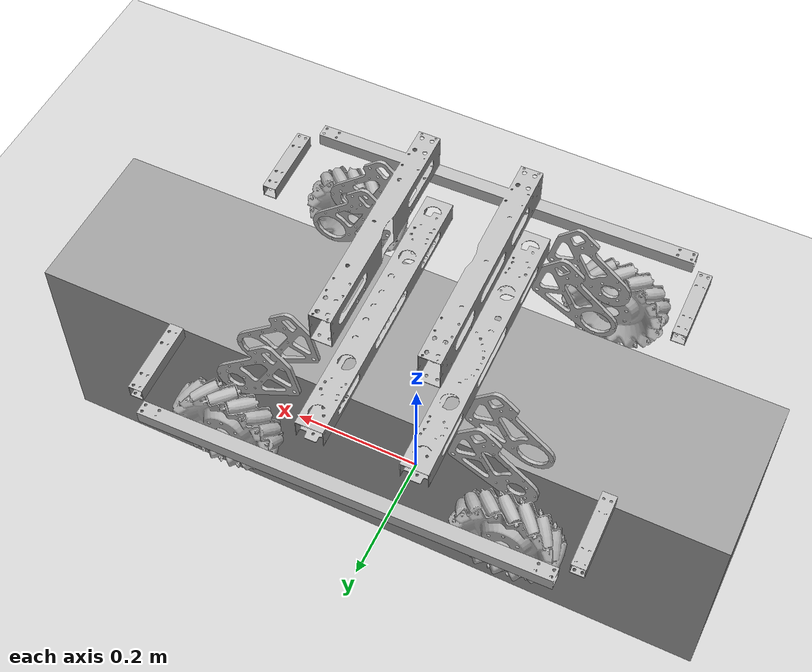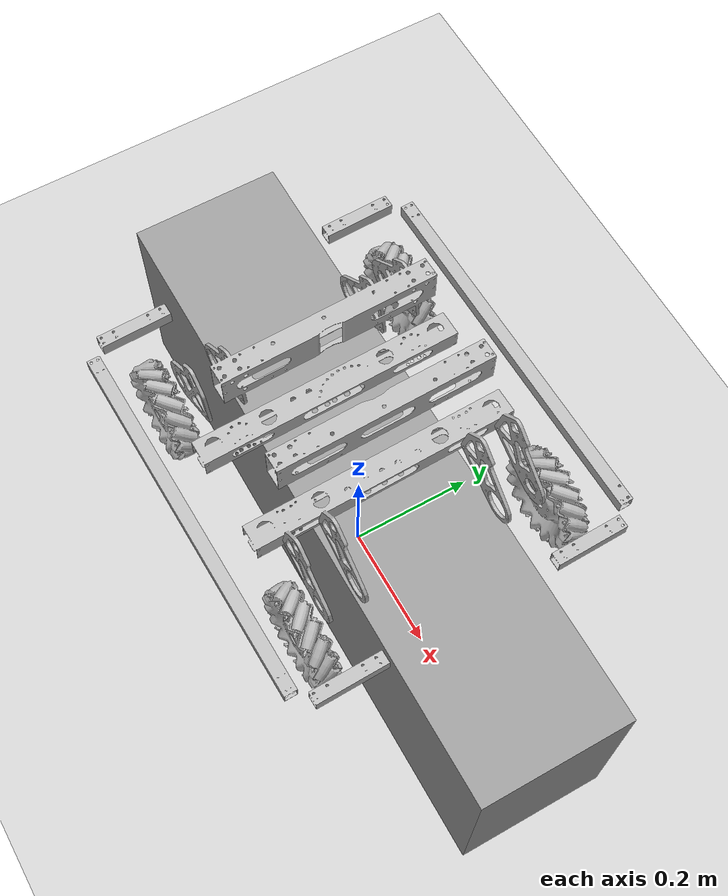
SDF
<sdf version="1.7">
 <world name="default">
  <physics type="ode">
   <max_step_size>0.001</max_step_size>
   <real_time_update_rate>1000</real_time_update_rate>
   <real_time_factor>1</real_time_factor>
  </physics>
  <light name="sun" type="directional">
   <pose>0 0 10 0 -0 0</pose>
   <diffuse>0.8 0.8 0.8 1</diffuse>
   <specular>0.2 0.2 0.2 1</specular>
   <attenuation>
    <range>1000</range>
    <constant>0.9</constant>
    <linear>0.01</linear>
    <quadratic>0.001</quadratic>
   </attenuation>
   <direction>-0.5 0.1 -0.9</direction>
   <spot><inner_angle>0</inner_angle><outer_angle>0</outer_angle><falloff>0</falloff></spot>
  </light>
  <model name="ground_plane">
   <static>1</static>
   <link name="link">
    <collision name="collision">
     <geometry><plane><normal>0 0 1</normal><size>100 100</size></plane></geometry>
     <surface>
      <contact><collide_bitmask>65535</collide_bitmask></contact>
      <friction><ode><mu>100</mu><mu2>50</mu2></ode></friction>
     </surface>
    </collision>
    <visual name="visual">
     <cast_shadows>0</cast_shadows>
     <geometry><plane><normal>0 0 1</normal><size>100 100</size></plane></geometry>
     <material>
      <script><uri>file://media/materials/scripts/gazebo.material</uri><name>Gazebo/Grey</name></script>
     </material>
    </visual>
   </link>
  </model>
  <gravity>0 0 -9.8</gravity>
  <magnetic_field>6e-06 2.3e-05 -4.2e-05</magnetic_field>
  <atmosphere type="adiabatic"/>
  <scene><ambient>0.4 0.4 0.4 1</ambient><background>0.7 0.7 0.7 1</background><shadows>1</shadows></scene>
  <spherical_coordinates>
   <surface_model>EARTH_WGS84</surface_model>
   <latitude_deg>0</latitude_deg>
   <longitude_deg>0</longitude_deg>
   <elevation>0</elevation>
   <heading_deg>0</heading_deg>
  </spherical_coordinates>
  <model name="hero">
   <link name="base_link">
    <inertial>
     <pose>-0.003691 -0.001885 0.024404 0 -0 0</pose>
     <mass>10.3427</mass>
     <inertia>
      <ixx>0.1952</ixx>
      <ixy>-0.001504</ixy>
      <ixz>0.005871</ixz>
      <iyy>0.3011</iyy>
      <iyz>-0.001077</iyz>
      <izz>0.4074</izz>
     </inertia>
    </inertial>
    <collision name="base_link_collision">
     <geometry>
      <mesh>
       <scale>0.001 0.001 0.001</scale>
       <uri>/home/wiselook/RM/final_trial/rm_ws/src/rm_description_for_task/meshes/hero/base.stl</uri>
      </mesh>
     </geometry>
    </collision>
    <visual name="base_link_visual">
     <geometry>
      <mesh>
       <scale>0.001 0.001 0.001</scale>
       <uri>/home/wiselook/RM/final_trial/rm_ws/src/rm_description_for_task/meshes/hero/base.stl</uri>
      </mesh>
     </geometry>
    </visual>
   </link>
   <joint name="left_back_wheel_joint" type="revolute">
    <pose relative_to="base_link">-0.2 0.2 -0.068374 0 -0 0</pose>
    <parent>base_link</parent>
    <child>left_back_wheel</child>
    <axis>
     <xyz>0 1 0</xyz>
     <limit><lower>-1e+09</lower><upper>1e+09</upper><effort>5</effort><velocity>50</velocity></limit>
     <dynamics>
      <damping>0</damping>
      <friction>0.05</friction>
      <spring_reference>0</spring_reference>
      <spring_stiffness>0</spring_stiffness>
     </dynamics>
    </axis>
   </joint>
   <link name="left_back_wheel">
    <pose relative_to="left_back_wheel_joint">0 0 0 0 -0 0</pose>
    <inertial>
     <mass>0.59</mass>
     <inertia>
      <ixx>0.001416</ixx>
      <ixy>0</ixy>
      <ixz>0</ixz>
      <iyy>0.002749</iyy>
      <iyz>0</iyz>
      <izz>0.001416</izz>
     </inertia>
    </inertial>
    <visual name="left_back_wheel_visual">
     <geometry>
      <mesh>
       <scale>0.001 0.001 0.001</scale>
       <uri>/home/wiselook/RM/final_trial/rm_ws/src/rm_description_for_task/meshes/common/left_threaded_mecanum_wheel.stl</uri>
      </mesh>
     </geometry>
    </visual>
   </link>
   <joint name="left_back_roller_0_joint" type="revolute">
    <pose relative_to="left_back_wheel">0 0 -0.06725 0 -0 0</pose>
    <parent>left_back_wheel</parent>
    <child>left_back_roller_0</child>
    <axis>
     <xyz>0.707107 0.707107 0</xyz>
     <limit><lower>-1e+16</lower><upper>1e+16</upper></limit>
     <dynamics>
      <damping>0</damping>
      <friction>0.001</friction>
      <spring_reference>0</spring_reference>
      <spring_stiffness>0</spring_stiffness>
     </dynamics>
    </axis>
   </joint>
   <link name="left_back_roller_0">
    <pose relative_to="left_back_roller_0_joint">0 0 0 0 -0 0</pose>
    <inertial>
     <mass>0.036</mass>
     <inertia>
      <ixx>3.128e-06</ixx>
      <ixy>0</ixy>
      <ixz>0</ixz>
      <iyy>3.128e-06</iyy>
      <iyz>0</iyz>
      <izz>3.128e-06</izz>
     </inertia>
    </inertial>
    <collision name="left_back_roller_0_collision">
     <pose>0 0 0 0 -0 0.785398</pose>
     <geometry>
      <mesh>
       <scale>0.001 0.001 0.001</scale>
       <uri>/home/wiselook/RM/final_trial/rm_ws/src/rm_description_for_task/meshes/common/roller.stl</uri>
      </mesh>
     </geometry>
     <surface>
      <contact><ode><kp>1e+06</kp><kd>100</kd></ode></contact>
      <friction><ode><mu>2000</mu><mu2>2000</mu2></ode></friction>
     </surface>
    </collision>
   </link>
   <joint name="left_back_roller_10_joint" type="revolute">
    <pose relative_to="left_back_wheel">-0.047696 0 0.04741 0 -0 0</pose>
    <parent>left_back_wheel</parent>
    <child>left_back_roller_10</child>
    <axis>
     <xyz>-0.498493 0.707107 -0.501502</xyz>
     <limit><lower>-1e+16</lower><upper>1e+16</upper></limit>
     <dynamics>
      <damping>0</damping>
      <friction>0.001</friction>
      <spring_reference>0</spring_reference>
      <spring_stiffness>0</spring_stiffness>
     </dynamics>
    </axis>
   </joint>
   <link name="left_back_roller_10">
    <pose relative_to="left_back_roller_10_joint">0 0 0 0 -0 0</pose>
    <inertial>
     <mass>0.036</mass>
     <inertia>
      <ixx>3.128e-06</ixx>
      <ixy>0</ixy>
      <ixz>0</ixz>
      <iyy>3.128e-06</iyy>
      <iyz>0</iyz>
      <izz>3.128e-06</izz>
     </inertia>
    </inertial>
    <collision name="left_back_roller_10_collision">
     <pose>0 0 0 0.956726 0.525334 2.18485</pose>
     <geometry>
      <mesh>
       <scale>0.001 0.001 0.001</scale>
       <uri>/home/wiselook/RM/final_trial/rm_ws/src/rm_description_for_task/meshes/common/roller.stl</uri>
      </mesh>
     </geometry>
     <surface>
      <contact><ode><kp>1e+06</kp><kd>100</kd></ode></contact>
      <friction><ode><mu>2000</mu><mu2>2000</mu2></ode></friction>
     </surface>
    </collision>
   </link>
   <joint name="left_back_roller_11_joint" type="revolute">
    <pose relative_to="left_back_wheel">-0.062216 0 0.02553 0 -0 0</pose>
    <parent>left_back_wheel</parent>
    <child>left_back_roller_11</child>
    <axis>
     <xyz>-0.268434 0.707107 -0.654174</xyz>
     <limit><lower>-1e+16</lower><upper>1e+16</upper></limit>
     <dynamics>
      <damping>0</damping>
      <friction>0.001</friction>
      <spring_reference>0</spring_reference>
      <spring_stiffness>0</spring_stiffness>
     </dynamics>
    </axis>
   </joint>
   <link name="left_back_roller_11">
    <pose relative_to="left_back_roller_11_joint">0 0 0 0 -0 0</pose>
    <inertial>
     <mass>0.036</mass>
     <inertia>
      <ixx>3.128e-06</ixx>
      <ixy>0</ixy>
      <ixz>0</ixz>
      <iyy>3.128e-06</iyy>
      <iyz>0</iyz>
      <izz>3.128e-06</izz>
     </inertia>
    </inertial>
    <collision name="left_back_roller_11_collision">
     <pose>0 0 0 0.989948 0.713089 1.93361</pose>
     <geometry>
      <mesh>
       <scale>0.001 0.001 0.001</scale>
       <uri>/home/wiselook/RM/final_trial/rm_ws/src/rm_description_for_task/meshes/common/roller.stl</uri>
      </mesh>
     </geometry>
     <surface>
      <contact><ode><kp>1e+06</kp><kd>100</kd></ode></contact>
      <friction><ode><mu>2000</mu><mu2>2000</mu2></ode></friction>
     </surface>
    </collision>
   </link>
   <joint name="left_back_roller_12_joint" type="revolute">
    <pose relative_to="left_back_wheel">-0.06725 0 -0.000243 0 -0 0</pose>
    <parent>left_back_wheel</parent>
    <child>left_back_roller_12</child>
    <axis>
     <xyz>0.002553 0.707107 -0.707102</xyz>
     <limit><lower>-1e+16</lower><upper>1e+16</upper></limit>
     <dynamics>
      <damping>0</damping>
      <friction>0.001</friction>
      <spring_reference>0</spring_reference>
      <spring_stiffness>0</spring_stiffness>
     </dynamics>
    </axis>
   </joint>
   <link name="left_back_roller_12">
    <pose relative_to="left_back_roller_12_joint">0 0 0 0 -0 0</pose>
    <inertial>
     <mass>0.036</mass>
     <inertia>
      <ixx>3.128e-06</ixx>
      <ixy>0</ixy>
      <ixz>0</ixz>
      <iyy>3.128e-06</iyy>
      <iyz>0</iyz>
      <izz>3.128e-06</izz>
     </inertia>
    </inertial>
    <collision name="left_back_roller_12_collision">
     <pose>0 0 0 0.782842 0.785392 1.56719</pose>
     <geometry>
      <mesh>
       <scale>0.001 0.001 0.001</scale>
       <uri>/home/wiselook/RM/final_trial/rm_ws/src/rm_description_for_task/meshes/common/roller.stl</uri>
      </mesh>
     </geometry>
     <surface>
      <contact><ode><kp>1e+06</kp><kd>100</kd></ode></contact>
      <friction><ode><mu>2000</mu><mu2>2000</mu2></ode></friction>
     </surface>
    </collision>
   </link>
   <joint name="left_back_roller_13_joint" type="revolute">
    <pose relative_to="left_back_wheel">-0.06203 0 -0.025978 0 -0 0</pose>
    <parent>left_back_wheel</parent>
    <child>left_back_roller_13</child>
    <axis>
     <xyz>0.273152 0.707107 -0.652218</xyz>
     <limit><lower>-1e+16</lower><upper>1e+16</upper></limit>
     <dynamics>
      <damping>0</damping>
      <friction>0.001</friction>
      <spring_reference>0</spring_reference>
      <spring_stiffness>0</spring_stiffness>
     </dynamics>
    </axis>
   </joint>
   <link name="left_back_roller_13">
    <pose relative_to="left_back_roller_13_joint">0 0 0 0 -0 0</pose>
    <inertial>
     <mass>0.036</mass>
     <inertia>
      <ixx>3.128e-06</ixx>
      <ixy>0</ixy>
      <ixz>0</ixz>
      <iyy>3.128e-06</iyy>
      <iyz>0</iyz>
      <izz>3.128e-06</izz>
     </inertia>
    </inertial>
    <collision name="left_back_roller_13_collision">
     <pose>0 0 0 0.498229 0.710507 1.20216</pose>
     <geometry>
      <mesh>
       <scale>0.001 0.001 0.001</scale>
       <uri>/home/wiselook/RM/final_trial/rm_ws/src/rm_description_for_task/meshes/common/roller.stl</uri>
      </mesh>
     </geometry>
     <surface>
      <contact><ode><kp>1e+06</kp><kd>100</kd></ode></contact>
      <friction><ode><mu>2000</mu><mu2>2000</mu2></ode></friction>
     </surface>
    </collision>
   </link>
   <joint name="left_back_roller_14_joint" type="revolute">
    <pose relative_to="left_back_wheel">-0.047352 0 -0.047753 0 -0 0</pose>
    <parent>left_back_wheel</parent>
    <child>left_back_roller_14</child>
    <axis>
     <xyz>0.502102 0.707107 -0.497889</xyz>
     <limit><lower>-1e+16</lower><upper>1e+16</upper></limit>
     <dynamics>
      <damping>0</damping>
      <friction>0.001</friction>
      <spring_reference>0</spring_reference>
      <spring_stiffness>0</spring_stiffness>
     </dynamics>
    </axis>
   </joint>
   <link name="left_back_roller_14">
    <pose relative_to="left_back_roller_14_joint">0 0 0 0 -0 0</pose>
    <inertial>
     <mass>0.036</mass>
     <inertia>
      <ixx>3.128e-06</ixx>
      <ixy>0</ixy>
      <ixz>0</ixz>
      <iyy>3.128e-06</iyy>
      <iyz>0</iyz>
      <izz>3.128e-06</izz>
     </inertia>
    </inertial>
    <collision name="left_back_roller_14_collision">
     <pose>0 0 0 0.273661 0.521163 0.953338</pose>
     <geometry>
      <mesh>
       <scale>0.001 0.001 0.001</scale>
       <uri>/home/wiselook/RM/final_trial/rm_ws/src/rm_description_for_task/meshes/common/roller.stl</uri>
      </mesh>
     </geometry>
     <surface>
      <contact><ode><kp>1e+06</kp><kd>100</kd></ode></contact>
      <friction><ode><mu>2000</mu><mu2>2000</mu2></ode></friction>
     </surface>
    </collision>
   </link>
   <joint name="left_back_roller_15_joint" type="revolute">
    <pose relative_to="left_back_wheel">-0.025455 0 -0.062246 0 -0 0</pose>
    <parent>left_back_wheel</parent>
    <child>left_back_roller_15</child>
    <axis>
     <xyz>0.654496 0.707107 -0.267647</xyz>
     <limit><lower>-1e+16</lower><upper>1e+16</upper></limit>
     <dynamics>
      <damping>0</damping>
      <friction>0.001</friction>
      <spring_reference>0</spring_reference>
      <spring_stiffness>0</spring_stiffness>
     </dynamics>
    </axis>
   </joint>
   <link name="left_back_roller_15">
    <pose relative_to="left_back_roller_15_joint">0 0 0 0 -0 0</pose>
    <inertial>
     <mass>0.036</mass>
     <inertia>
      <ixx>3.128e-06</ixx>
      <ixy>0</ixy>
      <ixz>0</ixz>
      <iyy>3.128e-06</iyy>
      <iyz>0</iyz>
      <izz>3.128e-06</izz>
     </inertia>
    </inertial>
    <collision name="left_back_roller_15_collision">
     <pose>0 0 0 0.119 0.27095 0.824018</pose>
     <geometry>
      <mesh>
       <scale>0.001 0.001 0.001</scale>
       <uri>/home/wiselook/RM/final_trial/rm_ws/src/rm_description_for_task/meshes/common/roller.stl</uri>
      </mesh>
     </geometry>
     <surface>
      <contact><ode><kp>1e+06</kp><kd>100</kd></ode></contact>
      <friction><ode><mu>2000</mu><mu2>2000</mu2></ode></friction>
     </surface>
    </collision>
   </link>
   <joint name="left_back_roller_1_joint" type="revolute">
    <pose relative_to="left_back_wheel">0.025754 0 -0.062123 0 -0 0</pose>
    <parent>left_back_wheel</parent>
    <child>left_back_roller_1</child>
    <axis>
     <xyz>0.6532 0.707107 0.270795</xyz>
     <limit><lower>-1e+16</lower><upper>1e+16</upper></limit>
     <dynamics>
      <damping>0</damping>
      <friction>0.001</friction>
      <spring_reference>0</spring_reference>
      <spring_stiffness>0</spring_stiffness>
     </dynamics>
    </axis>
   </joint>
   <link name="left_back_roller_1">
    <pose relative_to="left_back_roller_1_joint">0 0 0 0 -0 0</pose>
    <inertial>
     <mass>0.036</mass>
     <inertia>
      <ixx>3.128e-06</ixx>
      <ixy>0</ixy>
      <ixz>0</ixz>
      <iyy>3.128e-06</iyy>
      <iyz>0</iyz>
      <izz>3.128e-06</izz>
     </inertia>
    </inertial>
    <collision name="left_back_roller_1_collision">
     <pose>0 0 0 -0.120612 -0.274218 0.825006</pose>
     <geometry>
      <mesh>
       <scale>0.001 0.001 0.001</scale>
       <uri>/home/wiselook/RM/final_trial/rm_ws/src/rm_description_for_task/meshes/common/roller.stl</uri>
      </mesh>
     </geometry>
     <surface>
      <contact><ode><kp>1e+06</kp><kd>100</kd></ode></contact>
      <friction><ode><mu>2000</mu><mu2>2000</mu2></ode></friction>
     </surface>
    </collision>
   </link>
   <joint name="left_back_roller_2_joint" type="revolute">
    <pose relative_to="left_back_wheel">0.047582 0 -0.047524 0 -0 0</pose>
    <parent>left_back_wheel</parent>
    <child>left_back_roller_2</child>
    <axis>
     <xyz>0.499699 0.707107 0.500301</xyz>
     <limit><lower>-1e+16</lower><upper>1e+16</upper></limit>
     <dynamics>
      <damping>0</damping>
      <friction>0.001</friction>
      <spring_reference>0</spring_reference>
      <spring_stiffness>0</spring_stiffness>
     </dynamics>
    </axis>
   </joint>
   <link name="left_back_roller_2">
    <pose relative_to="left_back_roller_2_joint">0 0 0 0 -0 0</pose>
    <inertial>
     <mass>0.036</mass>
     <inertia>
      <ixx>3.128e-06</ixx>
      <ixy>0</ixy>
      <ixz>0</ixz>
      <iyy>3.128e-06</iyy>
      <iyz>0</iyz>
      <izz>3.128e-06</izz>
     </inertia>
    </inertial>
    <collision name="left_back_roller_2_collision">
     <pose>0 0 0 -0.275927 -0.523946 0.9556</pose>
     <geometry>
      <mesh>
       <scale>0.001 0.001 0.001</scale>
       <uri>/home/wiselook/RM/final_trial/rm_ws/src/rm_description_for_task/meshes/common/roller.stl</uri>
      </mesh>
     </geometry>
     <surface>
      <contact><ode><kp>1e+06</kp><kd>100</kd></ode></contact>
      <friction><ode><mu>2000</mu><mu2>2000</mu2></ode></friction>
     </surface>
    </collision>
   </link>
   <joint name="left_back_roller_3_joint" type="revolute">
    <pose relative_to="left_back_wheel">0.062154 0 -0.025679 0 -0 0</pose>
    <parent>left_back_wheel</parent>
    <child>left_back_roller_3</child>
    <axis>
     <xyz>0.270008 0.707107 0.653525</xyz>
     <limit><lower>-1e+16</lower><upper>1e+16</upper></limit>
     <dynamics>
      <damping>0</damping>
      <friction>0.001</friction>
      <spring_reference>0</spring_reference>
      <spring_stiffness>0</spring_stiffness>
     </dynamics>
    </axis>
   </joint>
   <link name="left_back_roller_3">
    <pose relative_to="left_back_roller_3_joint">0 0 0 0 -0 0</pose>
    <inertial>
     <mass>0.036</mass>
     <inertia>
      <ixx>3.128e-06</ixx>
      <ixy>0</ixy>
      <ixz>0</ixz>
      <iyy>3.128e-06</iyy>
      <iyz>0</iyz>
      <izz>3.128e-06</izz>
     </inertia>
    </inertial>
    <collision name="left_back_roller_3_collision">
     <pose>0 0 0 -0.501485 -0.712233 1.20603</pose>
     <geometry>
      <mesh>
       <scale>0.001 0.001 0.001</scale>
       <uri>/home/wiselook/RM/final_trial/rm_ws/src/rm_description_for_task/meshes/common/roller.stl</uri>
      </mesh>
     </geometry>
     <surface>
      <contact><ode><kp>1e+06</kp><kd>100</kd></ode></contact>
      <friction><ode><mu>2000</mu><mu2>2000</mu2></ode></friction>
     </surface>
    </collision>
   </link>
   <joint name="left_back_roller_4_joint" type="revolute">
    <pose relative_to="left_back_wheel">0.06725 0 8.1e-05 0 -0 0</pose>
    <parent>left_back_wheel</parent>
    <child>left_back_roller_4</child>
    <axis>
     <xyz>-0.000851 0.707107 0.707106</xyz>
     <limit><lower>-1e+16</lower><upper>1e+16</upper></limit>
     <dynamics>
      <damping>0</damping>
      <friction>0.001</friction>
      <spring_reference>0</spring_reference>
      <spring_stiffness>0</spring_stiffness>
     </dynamics>
    </axis>
   </joint>
   <link name="left_back_roller_4">
    <pose relative_to="left_back_roller_4_joint">0 0 0 0 -0 0</pose>
    <inertial>
     <mass>0.036</mass>
     <inertia>
      <ixx>3.128e-06</ixx>
      <ixy>0</ixy>
      <ixz>0</ixz>
      <iyy>3.128e-06</iyy>
      <iyz>0</iyz>
      <izz>3.128e-06</izz>
     </inertia>
    </inertial>
    <collision name="left_back_roller_4_collision">
     <pose>0 0 0 -0.786249 -0.785397 1.572</pose>
     <geometry>
      <mesh>
       <scale>0.001 0.001 0.001</scale>
       <uri>/home/wiselook/RM/final_trial/rm_ws/src/rm_description_for_task/meshes/common/roller.stl</uri>
      </mesh>
     </geometry>
     <surface>
      <contact><ode><kp>1e+06</kp><kd>100</kd></ode></contact>
      <friction><ode><mu>2000</mu><mu2>2000</mu2></ode></friction>
     </surface>
    </collision>
   </link>
   <joint name="left_back_roller_5_joint" type="revolute">
    <pose relative_to="left_back_wheel">0.062092 0 0.025829 0 -0 0</pose>
    <parent>left_back_wheel</parent>
    <child>left_back_roller_5</child>
    <axis>
     <xyz>-0.271581 0.707107 0.652874</xyz>
     <limit><lower>-1e+16</lower><upper>1e+16</upper></limit>
     <dynamics>
      <damping>0</damping>
      <friction>0.001</friction>
      <spring_reference>0</spring_reference>
      <spring_stiffness>0</spring_stiffness>
     </dynamics>
    </axis>
   </joint>
   <link name="left_back_roller_5">
    <pose relative_to="left_back_roller_5_joint">0 0 0 0 -0 0</pose>
    <inertial>
     <mass>0.036</mass>
     <inertia>
      <ixx>3.128e-06</ixx>
      <ixy>0</ixy>
      <ixz>0</ixz>
      <iyy>3.128e-06</iyy>
      <iyz>0</iyz>
      <izz>3.128e-06</izz>
     </inertia>
    </inertial>
    <collision name="left_back_roller_5_collision">
     <pose>0 0 0 -0.991227 -0.711372 1.9375</pose>
     <geometry>
      <mesh>
       <scale>0.001 0.001 0.001</scale>
       <uri>/home/wiselook/RM/final_trial/rm_ws/src/rm_description_for_task/meshes/common/roller.stl</uri>
      </mesh>
     </geometry>
     <surface>
      <contact><ode><kp>1e+06</kp><kd>100</kd></ode></contact>
      <friction><ode><mu>2000</mu><mu2>2000</mu2></ode></friction>
     </surface>
    </collision>
   </link>
   <joint name="left_back_roller_6_joint" type="revolute">
    <pose relative_to="left_back_wheel">0.047467 0 0.047639 0 -0 0</pose>
    <parent>left_back_wheel</parent>
    <child>left_back_roller_6</child>
    <axis>
     <xyz>-0.500902 0.707107 0.499096</xyz>
     <limit><lower>-1e+16</lower><upper>1e+16</upper></limit>
     <dynamics>
      <damping>0</damping>
      <friction>0.001</friction>
      <spring_reference>0</spring_reference>
      <spring_stiffness>0</spring_stiffness>
     </dynamics>
    </axis>
   </joint>
   <link name="left_back_roller_6">
    <pose relative_to="left_back_roller_6_joint">0 0 0 0 -0 0</pose>
    <inertial>
     <mass>0.036</mass>
     <inertia>
      <ixx>3.128e-06</ixx>
      <ixy>0</ixy>
      <ixz>0</ixz>
      <iyy>3.128e-06</iyy>
      <iyz>0</iyz>
      <izz>3.128e-06</izz>
     </inertia>
    </inertial>
    <collision name="left_back_roller_6_collision">
     <pose>0 0 0 -0.954462 -0.522556 2.18713</pose>
     <geometry>
      <mesh>
       <scale>0.001 0.001 0.001</scale>
       <uri>/home/wiselook/RM/final_trial/rm_ws/src/rm_description_for_task/meshes/common/roller.stl</uri>
      </mesh>
     </geometry>
     <surface>
      <contact><ode><kp>1e+06</kp><kd>100</kd></ode></contact>
      <friction><ode><mu>2000</mu><mu2>2000</mu2></ode></friction>
     </surface>
    </collision>
   </link>
   <joint name="left_back_roller_7_joint" type="revolute">
    <pose relative_to="left_back_wheel">0.025605 0 0.062185 0 -0 0</pose>
    <parent>left_back_wheel</parent>
    <child>left_back_roller_7</child>
    <axis>
     <xyz>-0.65385 0.707107 0.269221</xyz>
     <limit><lower>-1e+16</lower><upper>1e+16</upper></limit>
     <dynamics>
      <damping>0</damping>
      <friction>0.001</friction>
      <spring_reference>0</spring_reference>
      <spring_stiffness>0</spring_stiffness>
     </dynamics>
    </axis>
   </joint>
   <link name="left_back_roller_7">
    <pose relative_to="left_back_roller_7_joint">0 0 0 0 -0 0</pose>
    <inertial>
     <mass>0.036</mass>
     <inertia>
      <ixx>3.128e-06</ixx>
      <ixy>0</ixy>
      <ixz>0</ixz>
      <iyy>3.128e-06</iyy>
      <iyz>0</iyz>
      <izz>3.128e-06</izz>
     </inertia>
    </inertial>
    <collision name="left_back_roller_7_collision">
     <pose>0 0 0 -0.607775 -0.272584 2.31708</pose>
     <geometry>
      <mesh>
       <scale>0.001 0.001 0.001</scale>
       <uri>/home/wiselook/RM/final_trial/rm_ws/src/rm_description_for_task/meshes/common/roller.stl</uri>
      </mesh>
     </geometry>
     <surface>
      <contact><ode><kp>1e+06</kp><kd>100</kd></ode></contact>
      <friction><ode><mu>2000</mu><mu2>2000</mu2></ode></friction>
     </surface>
    </collision>
   </link>
   <joint name="left_back_roller_8_joint" type="revolute">
    <pose relative_to="left_back_wheel">-0.000162 0 0.06725 0 -0 0</pose>
    <parent>left_back_wheel</parent>
    <child>left_back_roller_8</child>
    <axis>
     <xyz>-0.707105 0.707107 -0.001702</xyz>
     <limit><lower>-1e+16</lower><upper>1e+16</upper></limit>
     <dynamics>
      <damping>0</damping>
      <friction>0.001</friction>
      <spring_reference>0</spring_reference>
      <spring_stiffness>0</spring_stiffness>
     </dynamics>
    </axis>
   </joint>
   <link name="left_back_roller_8">
    <pose relative_to="left_back_roller_8_joint">0 0 0 0 -0 0</pose>
    <inertial>
     <mass>0.036</mass>
     <inertia>
      <ixx>3.128e-06</ixx>
      <ixy>0</ixy>
      <ixz>0</ixz>
      <iyy>3.128e-06</iyy>
      <iyz>0</iyz>
      <izz>3.128e-06</izz>
     </inertia>
    </inertial>
    <collision name="left_back_roller_8_collision">
     <pose>0 0 0 0.00411 0.001702 2.35619</pose>
     <geometry>
      <mesh>
       <scale>0.001 0.001 0.001</scale>
       <uri>/home/wiselook/RM/final_trial/rm_ws/src/rm_description_for_task/meshes/common/roller.stl</uri>
      </mesh>
     </geometry>
     <surface>
      <contact><ode><kp>1e+06</kp><kd>100</kd></ode></contact>
      <friction><ode><mu>2000</mu><mu2>2000</mu2></ode></friction>
     </surface>
    </collision>
   </link>
   <joint name="left_back_roller_9_joint" type="revolute">
    <pose relative_to="left_back_wheel">-0.025904 0 0.062061 0 -0 0</pose>
    <parent>left_back_wheel</parent>
    <child>left_back_roller_9</child>
    <axis>
     <xyz>-0.652546 0.707107 -0.272366</xyz>
     <limit><lower>-1e+16</lower><upper>1e+16</upper></limit>
     <dynamics>
      <damping>0</damping>
      <friction>0.001</friction>
      <spring_reference>0</spring_reference>
      <spring_stiffness>0</spring_stiffness>
     </dynamics>
    </axis>
   </joint>
   <link name="left_back_roller_9">
    <pose relative_to="left_back_roller_9_joint">0 0 0 0 -0 0</pose>
    <inertial>
     <mass>0.036</mass>
     <inertia>
      <ixx>3.128e-06</ixx>
      <ixy>0</ixy>
      <ixz>0</ixz>
      <iyy>3.128e-06</iyy>
      <iyz>0</iyz>
      <izz>3.128e-06</izz>
     </inertia>
    </inertial>
    <collision name="left_back_roller_9_collision">
     <pose>0 0 0 0.613918 0.275851 2.31609</pose>
     <geometry>
      <mesh>
       <scale>0.001 0.001 0.001</scale>
       <uri>/home/wiselook/RM/final_trial/rm_ws/src/rm_description_for_task/meshes/common/roller.stl</uri>
      </mesh>
     </geometry>
     <surface>
      <contact><ode><kp>1e+06</kp><kd>100</kd></ode></contact>
      <friction><ode><mu>2000</mu><mu2>2000</mu2></ode></friction>
     </surface>
    </collision>
   </link>
   <joint name="left_front_wheel_joint" type="revolute">
    <pose relative_to="base_link">0.2 0.2 -0.068374 0 -0 0</pose>
    <parent>base_link</parent>
    <child>left_front_wheel</child>
    <axis>
     <xyz>0 1 0</xyz>
     <limit><lower>-1e+09</lower><upper>1e+09</upper><effort>5</effort><velocity>50</velocity></limit>
     <dynamics>
      <damping>0</damping>
      <friction>0.05</friction>
      <spring_reference>0</spring_reference>
      <spring_stiffness>0</spring_stiffness>
     </dynamics>
    </axis>
   </joint>
   <link name="left_front_wheel">
    <pose relative_to="left_front_wheel_joint">0 0 0 0 -0 0</pose>
    <inertial>
     <mass>0.59</mass>
     <inertia>
      <ixx>0.001416</ixx>
      <ixy>0</ixy>
      <ixz>0</ixz>
      <iyy>0.002749</iyy>
      <iyz>0</iyz>
      <izz>0.001416</izz>
     </inertia>
    </inertial>
    <visual name="left_front_wheel_visual">
     <geometry>
      <mesh>
       <scale>0.001 0.001 0.001</scale>
       <uri>/home/wiselook/RM/final_trial/rm_ws/src/rm_description_for_task/meshes/common/right_threaded_mecanum_wheel.stl</uri>
      </mesh>
     </geometry>
    </visual>
   </link>
   <joint name="left_front_roller_0_joint" type="revolute">
    <pose relative_to="left_front_wheel">0 0 -0.06725 0 -0 0</pose>
    <parent>left_front_wheel</parent>
    <child>left_front_roller_0</child>
    <axis>
     <xyz>0.707107 -0.707107 0</xyz>
     <limit><lower>-1e+16</lower><upper>1e+16</upper></limit>
     <dynamics>
      <damping>0</damping>
      <friction>0.001</friction>
      <spring_reference>0</spring_reference>
      <spring_stiffness>0</spring_stiffness>
     </dynamics>
    </axis>
   </joint>
   <link name="left_front_roller_0">
    <pose relative_to="left_front_roller_0_joint">0 0 0 0 -0 0</pose>
    <inertial>
     <mass>0.036</mass>
     <inertia>
      <ixx>3.128e-06</ixx>
      <ixy>0</ixy>
      <ixz>0</ixz>
      <iyy>3.128e-06</iyy>
      <iyz>0</iyz>
      <izz>3.128e-06</izz>
     </inertia>
    </inertial>
    <collision name="left_front_roller_0_collision">
     <pose>0 0 0 0 0 -0.785398</pose>
     <geometry>
      <mesh>
       <scale>0.001 0.001 0.001</scale>
       <uri>/home/wiselook/RM/final_trial/rm_ws/src/rm_description_for_task/meshes/common/roller.stl</uri>
      </mesh>
     </geometry>
     <surface>
      <contact><ode><kp>1e+06</kp><kd>100</kd></ode></contact>
      <friction><ode><mu>2000</mu><mu2>2000</mu2></ode></friction>
     </surface>
    </collision>
   </link>
   <joint name="left_front_roller_10_joint" type="revolute">
    <pose relative_to="left_front_wheel">-0.047696 0 0.04741 0 -0 0</pose>
    <parent>left_front_wheel</parent>
    <child>left_front_roller_10</child>
    <axis>
     <xyz>-0.498493 -0.707107 -0.501502</xyz>
     <limit><lower>-1e+16</lower><upper>1e+16</upper></limit>
     <dynamics>
      <damping>0</damping>
      <friction>0.001</friction>
      <spring_reference>0</spring_reference>
      <spring_stiffness>0</spring_stiffness>
     </dynamics>
    </axis>
   </joint>
   <link name="left_front_roller_10">
    <pose relative_to="left_front_roller_10_joint">0 0 0 0 -0 0</pose>
    <inertial>
     <mass>0.036</mass>
     <inertia>
      <ixx>3.128e-06</ixx>
      <ixy>0</ixy>
      <ixz>0</ixz>
      <iyy>3.128e-06</iyy>
      <iyz>0</iyz>
      <izz>3.128e-06</izz>
     </inertia>
    </inertial>
    <collision name="left_front_roller_10_collision">
     <pose>0 0 0 -0.956726 0.525334 -2.18485</pose>
     <geometry>
      <mesh>
       <scale>0.001 0.001 0.001</scale>
       <uri>/home/wiselook/RM/final_trial/rm_ws/src/rm_description_for_task/meshes/common/roller.stl</uri>
      </mesh>
     </geometry>
     <surface>
      <contact><ode><kp>1e+06</kp><kd>100</kd></ode></contact>
      <friction><ode><mu>2000</mu><mu2>2000</mu2></ode></friction>
     </surface>
    </collision>
   </link>
   <joint name="left_front_roller_11_joint" type="revolute">
    <pose relative_to="left_front_wheel">-0.062216 0 0.02553 0 -0 0</pose>
    <parent>left_front_wheel</parent>
    <child>left_front_roller_11</child>
    <axis>
     <xyz>-0.268434 -0.707107 -0.654174</xyz>
     <limit><lower>-1e+16</lower><upper>1e+16</upper></limit>
     <dynamics>
      <damping>0</damping>
      <friction>0.001</friction>
      <spring_reference>0</spring_reference>
      <spring_stiffness>0</spring_stiffness>
     </dynamics>
    </axis>
   </joint>
   <link name="left_front_roller_11">
    <pose relative_to="left_front_roller_11_joint">0 0 0 0 -0 0</pose>
    <inertial>
     <mass>0.036</mass>
     <inertia>
      <ixx>3.128e-06</ixx>
      <ixy>0</ixy>
      <ixz>0</ixz>
      <iyy>3.128e-06</iyy>
      <iyz>0</iyz>
      <izz>3.128e-06</izz>
     </inertia>
    </inertial>
    <collision name="left_front_roller_11_collision">
     <pose>0 0 0 -0.989948 0.713089 -1.93361</pose>
     <geometry>
      <mesh>
       <scale>0.001 0.001 0.001</scale>
       <uri>/home/wiselook/RM/final_trial/rm_ws/src/rm_description_for_task/meshes/common/roller.stl</uri>
      </mesh>
     </geometry>
     <surface>
      <contact><ode><kp>1e+06</kp><kd>100</kd></ode></contact>
      <friction><ode><mu>2000</mu><mu2>2000</mu2></ode></friction>
     </surface>
    </collision>
   </link>
   <joint name="left_front_roller_12_joint" type="revolute">
    <pose relative_to="left_front_wheel">-0.06725 0 -0.000243 0 -0 0</pose>
    <parent>left_front_wheel</parent>
    <child>left_front_roller_12</child>
    <axis>
     <xyz>0.002553 -0.707107 -0.707102</xyz>
     <limit><lower>-1e+16</lower><upper>1e+16</upper></limit>
     <dynamics>
      <damping>0</damping>
      <friction>0.001</friction>
      <spring_reference>0</spring_reference>
      <spring_stiffness>0</spring_stiffness>
     </dynamics>
    </axis>
   </joint>
   <link name="left_front_roller_12">
    <pose relative_to="left_front_roller_12_joint">0 0 0 0 -0 0</pose>
    <inertial>
     <mass>0.036</mass>
     <inertia>
      <ixx>3.128e-06</ixx>
      <ixy>0</ixy>
      <ixz>0</ixz>
      <iyy>3.128e-06</iyy>
      <iyz>0</iyz>
      <izz>3.128e-06</izz>
     </inertia>
    </inertial>
    <collision name="left_front_roller_12_collision">
     <pose>0 0 0 -0.782842 0.785392 -1.56719</pose>
     <geometry>
      <mesh>
       <scale>0.001 0.001 0.001</scale>
       <uri>/home/wiselook/RM/final_trial/rm_ws/src/rm_description_for_task/meshes/common/roller.stl</uri>
      </mesh>
     </geometry>
     <surface>
      <contact><ode><kp>1e+06</kp><kd>100</kd></ode></contact>
      <friction><ode><mu>2000</mu><mu2>2000</mu2></ode></friction>
     </surface>
    </collision>
   </link>
   <joint name="left_front_roller_13_joint" type="revolute">
    <pose relative_to="left_front_wheel">-0.06203 0 -0.025978 0 -0 0</pose>
    <parent>left_front_wheel</parent>
    <child>left_front_roller_13</child>
    <axis>
     <xyz>0.273152 -0.707107 -0.652218</xyz>
     <limit><lower>-1e+16</lower><upper>1e+16</upper></limit>
     <dynamics>
      <damping>0</damping>
      <friction>0.001</friction>
      <spring_reference>0</spring_reference>
      <spring_stiffness>0</spring_stiffness>
     </dynamics>
    </axis>
   </joint>
   <link name="left_front_roller_13">
    <pose relative_to="left_front_roller_13_joint">0 0 0 0 -0 0</pose>
    <inertial>
     <mass>0.036</mass>
     <inertia>
      <ixx>3.128e-06</ixx>
      <ixy>0</ixy>
      <ixz>0</ixz>
      <iyy>3.128e-06</iyy>
      <iyz>0</iyz>
      <izz>3.128e-06</izz>
     </inertia>
    </inertial>
    <collision name="left_front_roller_13_collision">
     <pose>0 0 0 -0.498229 0.710507 -1.20216</pose>
     <geometry>
      <mesh>
       <scale>0.001 0.001 0.001</scale>
       <uri>/home/wiselook/RM/final_trial/rm_ws/src/rm_description_for_task/meshes/common/roller.stl</uri>
      </mesh>
     </geometry>
     <surface>
      <contact><ode><kp>1e+06</kp><kd>100</kd></ode></contact>
      <friction><ode><mu>2000</mu><mu2>2000</mu2></ode></friction>
     </surface>
    </collision>
   </link>
   <joint name="left_front_roller_14_joint" type="revolute">
    <pose relative_to="left_front_wheel">-0.047352 0 -0.047753 0 -0 0</pose>
    <parent>left_front_wheel</parent>
    <child>left_front_roller_14</child>
    <axis>
     <xyz>0.502102 -0.707107 -0.497889</xyz>
     <limit><lower>-1e+16</lower><upper>1e+16</upper></limit>
     <dynamics>
      <damping>0</damping>
      <friction>0.001</friction>
      <spring_reference>0</spring_reference>
      <spring_stiffness>0</spring_stiffness>
     </dynamics>
    </axis>
   </joint>
   <link name="left_front_roller_14">
    <pose relative_to="left_front_roller_14_joint">0 0 0 0 -0 0</pose>
    <inertial>
     <mass>0.036</mass>
     <inertia>
      <ixx>3.128e-06</ixx>
      <ixy>0</ixy>
      <ixz>0</ixz>
      <iyy>3.128e-06</iyy>
      <iyz>0</iyz>
      <izz>3.128e-06</izz>
     </inertia>
    </inertial>
    <collision name="left_front_roller_14_collision">
     <pose>0 0 0 -0.273661 0.521163 -0.953338</pose>
     <geometry>
      <mesh>
       <scale>0.001 0.001 0.001</scale>
       <uri>/home/wiselook/RM/final_trial/rm_ws/src/rm_description_for_task/meshes/common/roller.stl</uri>
      </mesh>
     </geometry>
     <surface>
      <contact><ode><kp>1e+06</kp><kd>100</kd></ode></contact>
      <friction><ode><mu>2000</mu><mu2>2000</mu2></ode></friction>
     </surface>
    </collision>
   </link>
   <joint name="left_front_roller_15_joint" type="revolute">
    <pose relative_to="left_front_wheel">-0.025455 0 -0.062246 0 -0 0</pose>
    <parent>left_front_wheel</parent>
    <child>left_front_roller_15</child>
    <axis>
     <xyz>0.654496 -0.707107 -0.267647</xyz>
     <limit><lower>-1e+16</lower><upper>1e+16</upper></limit>
     <dynamics>
      <damping>0</damping>
      <friction>0.001</friction>
      <spring_reference>0</spring_reference>
      <spring_stiffness>0</spring_stiffness>
     </dynamics>
    </axis>
   </joint>
   <link name="left_front_roller_15">
    <pose relative_to="left_front_roller_15_joint">0 0 0 0 -0 0</pose>
    <inertial>
     <mass>0.036</mass>
     <inertia>
      <ixx>3.128e-06</ixx>
      <ixy>0</ixy>
      <ixz>0</ixz>
      <iyy>3.128e-06</iyy>
      <iyz>0</iyz>
      <izz>3.128e-06</izz>
     </inertia>
    </inertial>
    <collision name="left_front_roller_15_collision">
     <pose>0 0 0 -0.119 0.27095 -0.824018</pose>
     <geometry>
      <mesh>
       <scale>0.001 0.001 0.001</scale>
       <uri>/home/wiselook/RM/final_trial/rm_ws/src/rm_description_for_task/meshes/common/roller.stl</uri>
      </mesh>
     </geometry>
     <surface>
      <contact><ode><kp>1e+06</kp><kd>100</kd></ode></contact>
      <friction><ode><mu>2000</mu><mu2>2000</mu2></ode></friction>
     </surface>
    </collision>
   </link>
   <joint name="left_front_roller_1_joint" type="revolute">
    <pose relative_to="left_front_wheel">0.025754 0 -0.062123 0 -0 0</pose>
    <parent>left_front_wheel</parent>
    <child>left_front_roller_1</child>
    <axis>
     <xyz>0.6532 -0.707107 0.270795</xyz>
     <limit><lower>-1e+16</lower><upper>1e+16</upper></limit>
     <dynamics>
      <damping>0</damping>
      <friction>0.001</friction>
      <spring_reference>0</spring_reference>
      <spring_stiffness>0</spring_stiffness>
     </dynamics>
    </axis>
   </joint>
   <link name="left_front_roller_1">
    <pose relative_to="left_front_roller_1_joint">0 0 0 0 -0 0</pose>
    <inertial>
     <mass>0.036</mass>
     <inertia>
      <ixx>3.128e-06</ixx>
      <ixy>0</ixy>
      <ixz>0</ixz>
      <iyy>3.128e-06</iyy>
      <iyz>0</iyz>
      <izz>3.128e-06</izz>
     </inertia>
    </inertial>
    <collision name="left_front_roller_1_collision">
     <pose>0 0 0 0.120612 -0.274218 -0.825006</pose>
     <geometry>
      <mesh>
       <scale>0.001 0.001 0.001</scale>
       <uri>/home/wiselook/RM/final_trial/rm_ws/src/rm_description_for_task/meshes/common/roller.stl</uri>
      </mesh>
     </geometry>
     <surface>
      <contact><ode><kp>1e+06</kp><kd>100</kd></ode></contact>
      <friction><ode><mu>2000</mu><mu2>2000</mu2></ode></friction>
     </surface>
    </collision>
   </link>
   <joint name="left_front_roller_2_joint" type="revolute">
    <pose relative_to="left_front_wheel">0.047582 0 -0.047524 0 -0 0</pose>
    <parent>left_front_wheel</parent>
    <child>left_front_roller_2</child>
    <axis>
     <xyz>0.499699 -0.707107 0.500301</xyz>
     <limit><lower>-1e+16</lower><upper>1e+16</upper></limit>
     <dynamics>
      <damping>0</damping>
      <friction>0.001</friction>
      <spring_reference>0</spring_reference>
      <spring_stiffness>0</spring_stiffness>
     </dynamics>
    </axis>
   </joint>
   <link name="left_front_roller_2">
    <pose relative_to="left_front_roller_2_joint">0 0 0 0 -0 0</pose>
    <inertial>
     <mass>0.036</mass>
     <inertia>
      <ixx>3.128e-06</ixx>
      <ixy>0</ixy>
      <ixz>0</ixz>
      <iyy>3.128e-06</iyy>
      <iyz>0</iyz>
      <izz>3.128e-06</izz>
     </inertia>
    </inertial>
    <collision name="left_front_roller_2_collision">
     <pose>0 0 0 0.275927 -0.523946 -0.9556</pose>
     <geometry>
      <mesh>
       <scale>0.001 0.001 0.001</scale>
       <uri>/home/wiselook/RM/final_trial/rm_ws/src/rm_description_for_task/meshes/common/roller.stl</uri>
      </mesh>
     </geometry>
     <surface>
      <contact><ode><kp>1e+06</kp><kd>100</kd></ode></contact>
      <friction><ode><mu>2000</mu><mu2>2000</mu2></ode></friction>
     </surface>
    </collision>
   </link>
   <joint name="left_front_roller_3_joint" type="revolute">
    <pose relative_to="left_front_wheel">0.062154 0 -0.025679 0 -0 0</pose>
    <parent>left_front_wheel</parent>
    <child>left_front_roller_3</child>
    <axis>
     <xyz>0.270008 -0.707107 0.653525</xyz>
     <limit><lower>-1e+16</lower><upper>1e+16</upper></limit>
     <dynamics>
      <damping>0</damping>
      <friction>0.001</friction>
      <spring_reference>0</spring_reference>
      <spring_stiffness>0</spring_stiffness>
     </dynamics>
    </axis>
   </joint>
   <link name="left_front_roller_3">
    <pose relative_to="left_front_roller_3_joint">0 0 0 0 -0 0</pose>
    <inertial>
     <mass>0.036</mass>
     <inertia>
      <ixx>3.128e-06</ixx>
      <ixy>0</ixy>
      <ixz>0</ixz>
      <iyy>3.128e-06</iyy>
      <iyz>0</iyz>
      <izz>3.128e-06</izz>
     </inertia>
    </inertial>
    <collision name="left_front_roller_3_collision">
     <pose>0 0 0 0.501485 -0.712233 -1.20603</pose>
     <geometry>
      <mesh>
       <scale>0.001 0.001 0.001</scale>
       <uri>/home/wiselook/RM/final_trial/rm_ws/src/rm_description_for_task/meshes/common/roller.stl</uri>
      </mesh>
     </geometry>
     <surface>
      <contact><ode><kp>1e+06</kp><kd>100</kd></ode></contact>
      <friction><ode><mu>2000</mu><mu2>2000</mu2></ode></friction>
     </surface>
    </collision>
   </link>
   <joint name="left_front_roller_4_joint" type="revolute">
    <pose relative_to="left_front_wheel">0.06725 0 8.1e-05 0 -0 0</pose>
    <parent>left_front_wheel</parent>
    <child>left_front_roller_4</child>
    <axis>
     <xyz>-0.000851 -0.707107 0.707106</xyz>
     <limit><lower>-1e+16</lower><upper>1e+16</upper></limit>
     <dynamics>
      <damping>0</damping>
      <friction>0.001</friction>
      <spring_reference>0</spring_reference>
      <spring_stiffness>0</spring_stiffness>
     </dynamics>
    </axis>
   </joint>
   <link name="left_front_roller_4">
    <pose relative_to="left_front_roller_4_joint">0 0 0 0 -0 0</pose>
    <inertial>
     <mass>0.036</mass>
     <inertia>
      <ixx>3.128e-06</ixx>
      <ixy>0</ixy>
      <ixz>0</ixz>
      <iyy>3.128e-06</iyy>
      <iyz>0</iyz>
      <izz>3.128e-06</izz>
     </inertia>
    </inertial>
    <collision name="left_front_roller_4_collision">
     <pose>0 0 0 0.786249 -0.785397 -1.572</pose>
     <geometry>
      <mesh>
       <scale>0.001 0.001 0.001</scale>
       <uri>/home/wiselook/RM/final_trial/rm_ws/src/rm_description_for_task/meshes/common/roller.stl</uri>
      </mesh>
     </geometry>
     <surface>
      <contact><ode><kp>1e+06</kp><kd>100</kd></ode></contact>
      <friction><ode><mu>2000</mu><mu2>2000</mu2></ode></friction>
     </surface>
    </collision>
   </link>
   <joint name="left_front_roller_5_joint" type="revolute">
    <pose relative_to="left_front_wheel">0.062092 0 0.025829 0 -0 0</pose>
    <parent>left_front_wheel</parent>
    <child>left_front_roller_5</child>
    <axis>
     <xyz>-0.271581 -0.707107 0.652874</xyz>
     <limit><lower>-1e+16</lower><upper>1e+16</upper></limit>
     <dynamics>
      <damping>0</damping>
      <friction>0.001</friction>
      <spring_reference>0</spring_reference>
      <spring_stiffness>0</spring_stiffness>
     </dynamics>
    </axis>
   </joint>
   <link name="left_front_roller_5">
    <pose relative_to="left_front_roller_5_joint">0 0 0 0 -0 0</pose>
    <inertial>
     <mass>0.036</mass>
     <inertia>
      <ixx>3.128e-06</ixx>
      <ixy>0</ixy>
      <ixz>0</ixz>
      <iyy>3.128e-06</iyy>
      <iyz>0</iyz>
      <izz>3.128e-06</izz>
     </inertia>
    </inertial>
    <collision name="left_front_roller_5_collision">
     <pose>0 0 0 0.991227 -0.711372 -1.9375</pose>
     <geometry>
      <mesh>
       <scale>0.001 0.001 0.001</scale>
       <uri>/home/wiselook/RM/final_trial/rm_ws/src/rm_description_for_task/meshes/common/roller.stl</uri>
      </mesh>
     </geometry>
     <surface>
      <contact><ode><kp>1e+06</kp><kd>100</kd></ode></contact>
      <friction><ode><mu>2000</mu><mu2>2000</mu2></ode></friction>
     </surface>
    </collision>
   </link>
   <joint name="left_front_roller_6_joint" type="revolute">
    <pose relative_to="left_front_wheel">0.047467 0 0.047639 0 -0 0</pose>
    <parent>left_front_wheel</parent>
    <child>left_front_roller_6</child>
    <axis>
     <xyz>-0.500902 -0.707107 0.499096</xyz>
     <limit><lower>-1e+16</lower><upper>1e+16</upper></limit>
     <dynamics>
      <damping>0</damping>
      <friction>0.001</friction>
      <spring_reference>0</spring_reference>
      <spring_stiffness>0</spring_stiffness>
     </dynamics>
    </axis>
   </joint>
   <link name="left_front_roller_6">
    <pose relative_to="left_front_roller_6_joint">0 0 0 0 -0 0</pose>
    <inertial>
     <mass>0.036</mass>
     <inertia>
      <ixx>3.128e-06</ixx>
      <ixy>0</ixy>
      <ixz>0</ixz>
      <iyy>3.128e-06</iyy>
      <iyz>0</iyz>
      <izz>3.128e-06</izz>
     </inertia>
    </inertial>
    <collision name="left_front_roller_6_collision">
     <pose>0 0 0 0.954462 -0.522556 -2.18713</pose>
     <geometry>
      <mesh>
       <scale>0.001 0.001 0.001</scale>
       <uri>/home/wiselook/RM/final_trial/rm_ws/src/rm_description_for_task/meshes/common/roller.stl</uri>
      </mesh>
     </geometry>
     <surface>
      <contact><ode><kp>1e+06</kp><kd>100</kd></ode></contact>
      <friction><ode><mu>2000</mu><mu2>2000</mu2></ode></friction>
     </surface>
    </collision>
   </link>
   <joint name="left_front_roller_7_joint" type="revolute">
    <pose relative_to="left_front_wheel">0.025605 0 0.062185 0 -0 0</pose>
    <parent>left_front_wheel</parent>
    <child>left_front_roller_7</child>
    <axis>
     <xyz>-0.65385 -0.707107 0.269221</xyz>
     <limit><lower>-1e+16</lower><upper>1e+16</upper></limit>
     <dynamics>
      <damping>0</damping>
      <friction>0.001</friction>
      <spring_reference>0</spring_reference>
      <spring_stiffness>0</spring_stiffness>
     </dynamics>
    </axis>
   </joint>
   <link name="left_front_roller_7">
    <pose relative_to="left_front_roller_7_joint">0 0 0 0 -0 0</pose>
    <inertial>
     <mass>0.036</mass>
     <inertia>
      <ixx>3.128e-06</ixx>
      <ixy>0</ixy>
      <ixz>0</ixz>
      <iyy>3.128e-06</iyy>
      <iyz>0</iyz>
      <izz>3.128e-06</izz>
     </inertia>
    </inertial>
    <collision name="left_front_roller_7_collision">
     <pose>0 0 0 0.607775 -0.272584 -2.31708</pose>
     <geometry>
      <mesh>
       <scale>0.001 0.001 0.001</scale>
       <uri>/home/wiselook/RM/final_trial/rm_ws/src/rm_description_for_task/meshes/common/roller.stl</uri>
      </mesh>
     </geometry>
     <surface>
      <contact><ode><kp>1e+06</kp><kd>100</kd></ode></contact>
      <friction><ode><mu>2000</mu><mu2>2000</mu2></ode></friction>
     </surface>
    </collision>
   </link>
   <joint name="left_front_roller_8_joint" type="revolute">
    <pose relative_to="left_front_wheel">-0.000162 0 0.06725 0 -0 0</pose>
    <parent>left_front_wheel</parent>
    <child>left_front_roller_8</child>
    <axis>
     <xyz>-0.707105 -0.707107 -0.001702</xyz>
     <limit><lower>-1e+16</lower><upper>1e+16</upper></limit>
     <dynamics>
      <damping>0</damping>
      <friction>0.001</friction>
      <spring_reference>0</spring_reference>
      <spring_stiffness>0</spring_stiffness>
     </dynamics>
    </axis>
   </joint>
   <link name="left_front_roller_8">
    <pose relative_to="left_front_roller_8_joint">0 0 0 0 -0 0</pose>
    <inertial>
     <mass>0.036</mass>
     <inertia>
      <ixx>3.128e-06</ixx>
      <ixy>0</ixy>
      <ixz>0</ixz>
      <iyy>3.128e-06</iyy>
      <iyz>0</iyz>
      <izz>3.128e-06</izz>
     </inertia>
    </inertial>
    <collision name="left_front_roller_8_collision">
     <pose>0 0 0 -0.00411 0.001702 -2.35619</pose>
     <geometry>
      <mesh>
       <scale>0.001 0.001 0.001</scale>
       <uri>/home/wiselook/RM/final_trial/rm_ws/src/rm_description_for_task/meshes/common/roller.stl</uri>
      </mesh>
     </geometry>
     <surface>
      <contact><ode><kp>1e+06</kp><kd>100</kd></ode></contact>
      <friction><ode><mu>2000</mu><mu2>2000</mu2></ode></friction>
     </surface>
    </collision>
   </link>
   <joint name="left_front_roller_9_joint" type="revolute">
    <pose relative_to="left_front_wheel">-0.025904 0 0.062061 0 -0 0</pose>
    <parent>left_front_wheel</parent>
    <child>left_front_roller_9</child>
    <axis>
     <xyz>-0.652546 -0.707107 -0.272366</xyz>
     <limit><lower>-1e+16</lower><upper>1e+16</upper></limit>
     <dynamics>
      <damping>0</damping>
      <friction>0.001</friction>
      <spring_reference>0</spring_reference>
      <spring_stiffness>0</spring_stiffness>
     </dynamics>
    </axis>
   </joint>
   <link name="left_front_roller_9">
    <pose relative_to="left_front_roller_9_joint">0 0 0 0 -0 0</pose>
    <inertial>
     <mass>0.036</mass>
     <inertia>
      <ixx>3.128e-06</ixx>
      <ixy>0</ixy>
      <ixz>0</ixz>
      <iyy>3.128e-06</iyy>
      <iyz>0</iyz>
      <izz>3.128e-06</izz>
     </inertia>
    </inertial>
    <collision name="left_front_roller_9_collision">
     <pose>0 0 0 -0.613918 0.275851 -2.31609</pose>
     <geometry>
      <mesh>
       <scale>0.001 0.001 0.001</scale>
       <uri>/home/wiselook/RM/final_trial/rm_ws/src/rm_description_for_task/meshes/common/roller.stl</uri>
      </mesh>
     </geometry>
     <surface>
      <contact><ode><kp>1e+06</kp><kd>100</kd></ode></contact>
      <friction><ode><mu>2000</mu><mu2>2000</mu2></ode></friction>
     </surface>
    </collision>
   </link>
   <joint name="right_back_wheel_joint" type="revolute">
    <pose relative_to="base_link">-0.2 -0.2 -0.068374 0 -0 0</pose>
    <parent>base_link</parent>
    <child>right_back_wheel</child>
    <axis>
     <xyz>0 1 0</xyz>
     <limit><lower>-1e+09</lower><upper>1e+09</upper><effort>5</effort><velocity>50</velocity></limit>
     <dynamics>
      <damping>0</damping>
      <friction>0.05</friction>
      <spring_reference>0</spring_reference>
      <spring_stiffness>0</spring_stiffness>
     </dynamics>
    </axis>
   </joint>
   <link name="right_back_wheel">
    <pose relative_to="right_back_wheel_joint">0 0 0 0 -0 0</pose>
    <inertial>
     <mass>0.59</mass>
     <inertia>
      <ixx>0.001416</ixx>
      <ixy>0</ixy>
      <ixz>0</ixz>
      <iyy>0.002749</iyy>
      <iyz>0</iyz>
      <izz>0.001416</izz>
     </inertia>
    </inertial>
    <visual name="right_back_wheel_visual">
     <geometry>
      <mesh>
       <scale>0.001 0.001 0.001</scale>
       <uri>/home/wiselook/RM/final_trial/rm_ws/src/rm_description_for_task/meshes/common/right_threaded_mecanum_wheel.stl</uri>
      </mesh>
     </geometry>
    </visual>
   </link>
   <joint name="right_back_roller_0_joint" type="revolute">
    <pose relative_to="right_back_wheel">0 0 -0.06725 0 -0 0</pose>
    <parent>right_back_wheel</parent>
    <child>right_back_roller_0</child>
    <axis>
     <xyz>0.707107 -0.707107 0</xyz>
     <limit><lower>-1e+16</lower><upper>1e+16</upper></limit>
     <dynamics>
      <damping>0</damping>
      <friction>0.001</friction>
      <spring_reference>0</spring_reference>
      <spring_stiffness>0</spring_stiffness>
     </dynamics>
    </axis>
   </joint>
   <link name="right_back_roller_0">
    <pose relative_to="right_back_roller_0_joint">0 0 0 0 -0 0</pose>
    <inertial>
     <mass>0.036</mass>
     <inertia>
      <ixx>3.128e-06</ixx>
      <ixy>0</ixy>
      <ixz>0</ixz>
      <iyy>3.128e-06</iyy>
      <iyz>0</iyz>
      <izz>3.128e-06</izz>
     </inertia>
    </inertial>
    <collision name="right_back_roller_0_collision">
     <pose>0 0 0 0 0 -0.785398</pose>
     <geometry>
      <mesh>
       <scale>0.001 0.001 0.001</scale>
       <uri>/home/wiselook/RM/final_trial/rm_ws/src/rm_description_for_task/meshes/common/roller.stl</uri>
      </mesh>
     </geometry>
     <surface>
      <contact><ode><kp>1e+06</kp><kd>100</kd></ode></contact>
      <friction><ode><mu>2000</mu><mu2>2000</mu2></ode></friction>
     </surface>
    </collision>
   </link>
   <joint name="right_back_roller_10_joint" type="revolute">
    <pose relative_to="right_back_wheel">-0.047696 0 0.04741 0 -0 0</pose>
    <parent>right_back_wheel</parent>
    <child>right_back_roller_10</child>
    <axis>
     <xyz>-0.498493 -0.707107 -0.501502</xyz>
     <limit><lower>-1e+16</lower><upper>1e+16</upper></limit>
     <dynamics>
      <damping>0</damping>
      <friction>0.001</friction>
      <spring_reference>0</spring_reference>
      <spring_stiffness>0</spring_stiffness>
     </dynamics>
    </axis>
   </joint>
   <link name="right_back_roller_10">
    <pose relative_to="right_back_roller_10_joint">0 0 0 0 -0 0</pose>
    <inertial>
     <mass>0.036</mass>
     <inertia>
      <ixx>3.128e-06</ixx>
      <ixy>0</ixy>
      <ixz>0</ixz>
      <iyy>3.128e-06</iyy>
      <iyz>0</iyz>
      <izz>3.128e-06</izz>
     </inertia>
    </inertial>
    <collision name="right_back_roller_10_collision">
     <pose>0 0 0 -0.956726 0.525334 -2.18485</pose>
     <geometry>
      <mesh>
       <scale>0.001 0.001 0.001</scale>
       <uri>/home/wiselook/RM/final_trial/rm_ws/src/rm_description_for_task/meshes/common/roller.stl</uri>
      </mesh>
     </geometry>
     <surface>
      <contact><ode><kp>1e+06</kp><kd>100</kd></ode></contact>
      <friction><ode><mu>2000</mu><mu2>2000</mu2></ode></friction>
     </surface>
    </collision>
   </link>
   <joint name="right_back_roller_11_joint" type="revolute">
    <pose relative_to="right_back_wheel">-0.062216 0 0.02553 0 -0 0</pose>
    <parent>right_back_wheel</parent>
    <child>right_back_roller_11</child>
    <axis>
     <xyz>-0.268434 -0.707107 -0.654174</xyz>
     <limit><lower>-1e+16</lower><upper>1e+16</upper></limit>
     <dynamics>
      <damping>0</damping>
      <friction>0.001</friction>
      <spring_reference>0</spring_reference>
      <spring_stiffness>0</spring_stiffness>
     </dynamics>
    </axis>
   </joint>
   <link name="right_back_roller_11">
    <pose relative_to="right_back_roller_11_joint">0 0 0 0 -0 0</pose>
    <inertial>
     <mass>0.036</mass>
     <inertia>
      <ixx>3.128e-06</ixx>
      <ixy>0</ixy>
      <ixz>0</ixz>
      <iyy>3.128e-06</iyy>
      <iyz>0</iyz>
      <izz>3.128e-06</izz>
     </inertia>
    </inertial>
    <collision name="right_back_roller_11_collision">
     <pose>0 0 0 -0.989948 0.713089 -1.93361</pose>
     <geometry>
      <mesh>
       <scale>0.001 0.001 0.001</scale>
       <uri>/home/wiselook/RM/final_trial/rm_ws/src/rm_description_for_task/meshes/common/roller.stl</uri>
      </mesh>
     </geometry>
     <surface>
      <contact><ode><kp>1e+06</kp><kd>100</kd></ode></contact>
      <friction><ode><mu>2000</mu><mu2>2000</mu2></ode></friction>
     </surface>
    </collision>
   </link>
   <joint name="right_back_roller_12_joint" type="revolute">
    <pose relative_to="right_back_wheel">-0.06725 0 -0.000243 0 -0 0</pose>
    <parent>right_back_wheel</parent>
    <child>right_back_roller_12</child>
    <axis>
     <xyz>0.002553 -0.707107 -0.707102</xyz>
     <limit><lower>-1e+16</lower><upper>1e+16</upper></limit>
     <dynamics>
      <damping>0</damping>
      <friction>0.001</friction>
      <spring_reference>0</spring_reference>
      <spring_stiffness>0</spring_stiffness>
     </dynamics>
    </axis>
   </joint>
   <link name="right_back_roller_12">
    <pose relative_to="right_back_roller_12_joint">0 0 0 0 -0 0</pose>
    <inertial>
     <mass>0.036</mass>
     <inertia>
      <ixx>3.128e-06</ixx>
      <ixy>0</ixy>
      <ixz>0</ixz>
      <iyy>3.128e-06</iyy>
      <iyz>0</iyz>
      <izz>3.128e-06</izz>
     </inertia>
    </inertial>
    <collision name="right_back_roller_12_collision">
     <pose>0 0 0 -0.782842 0.785392 -1.56719</pose>
     <geometry>
      <mesh>
       <scale>0.001 0.001 0.001</scale>
       <uri>/home/wiselook/RM/final_trial/rm_ws/src/rm_description_for_task/meshes/common/roller.stl</uri>
      </mesh>
     </geometry>
     <surface>
      <contact><ode><kp>1e+06</kp><kd>100</kd></ode></contact>
      <friction><ode><mu>2000</mu><mu2>2000</mu2></ode></friction>
     </surface>
    </collision>
   </link>
   <joint name="right_back_roller_13_joint" type="revolute">
    <pose relative_to="right_back_wheel">-0.06203 0 -0.025978 0 -0 0</pose>
    <parent>right_back_wheel</parent>
    <child>right_back_roller_13</child>
    <axis>
     <xyz>0.273152 -0.707107 -0.652218</xyz>
     <limit><lower>-1e+16</lower><upper>1e+16</upper></limit>
     <dynamics>
      <damping>0</damping>
      <friction>0.001</friction>
      <spring_reference>0</spring_reference>
      <spring_stiffness>0</spring_stiffness>
     </dynamics>
    </axis>
   </joint>
   <link name="right_back_roller_13">
    <pose relative_to="right_back_roller_13_joint">0 0 0 0 -0 0</pose>
    <inertial>
     <mass>0.036</mass>
     <inertia>
      <ixx>3.128e-06</ixx>
      <ixy>0</ixy>
      <ixz>0</ixz>
      <iyy>3.128e-06</iyy>
      <iyz>0</iyz>
      <izz>3.128e-06</izz>
     </inertia>
    </inertial>
    <collision name="right_back_roller_13_collision">
     <pose>0 0 0 -0.498229 0.710507 -1.20216</pose>
     <geometry>
      <mesh>
       <scale>0.001 0.001 0.001</scale>
       <uri>/home/wiselook/RM/final_trial/rm_ws/src/rm_description_for_task/meshes/common/roller.stl</uri>
      </mesh>
     </geometry>
     <surface>
      <contact><ode><kp>1e+06</kp><kd>100</kd></ode></contact>
      <friction><ode><mu>2000</mu><mu2>2000</mu2></ode></friction>
     </surface>
    </collision>
   </link>
   <joint name="right_back_roller_14_joint" type="revolute">
    <pose relative_to="right_back_wheel">-0.047352 0 -0.047753 0 -0 0</pose>
    <parent>right_back_wheel</parent>
    <child>right_back_roller_14</child>
    <axis>
     <xyz>0.502102 -0.707107 -0.497889</xyz>
     <limit><lower>-1e+16</lower><upper>1e+16</upper></limit>
     <dynamics>
      <damping>0</damping>
      <friction>0.001</friction>
      <spring_reference>0</spring_reference>
      <spring_stiffness>0</spring_stiffness>
     </dynamics>
    </axis>
   </joint>
   <link name="right_back_roller_14">
    <pose relative_to="right_back_roller_14_joint">0 0 0 0 -0 0</pose>
    <inertial>
     <mass>0.036</mass>
     <inertia>
      <ixx>3.128e-06</ixx>
      <ixy>0</ixy>
      <ixz>0</ixz>
      <iyy>3.128e-06</iyy>
      <iyz>0</iyz>
      <izz>3.128e-06</izz>
     </inertia>
    </inertial>
    <collision name="right_back_roller_14_collision">
     <pose>0 0 0 -0.273661 0.521163 -0.953338</pose>
     <geometry>
      <mesh>
       <scale>0.001 0.001 0.001</scale>
       <uri>/home/wiselook/RM/final_trial/rm_ws/src/rm_description_for_task/meshes/common/roller.stl</uri>
      </mesh>
     </geometry>
     <surface>
      <contact><ode><kp>1e+06</kp><kd>100</kd></ode></contact>
      <friction><ode><mu>2000</mu><mu2>2000</mu2></ode></friction>
     </surface>
    </collision>
   </link>
   <joint name="right_back_roller_15_joint" type="revolute">
    <pose relative_to="right_back_wheel">-0.025455 0 -0.062246 0 -0 0</pose>
    <parent>right_back_wheel</parent>
    <child>right_back_roller_15</child>
    <axis>
     <xyz>0.654496 -0.707107 -0.267647</xyz>
     <limit><lower>-1e+16</lower><upper>1e+16</upper></limit>
     <dynamics>
      <damping>0</damping>
      <friction>0.001</friction>
      <spring_reference>0</spring_reference>
      <spring_stiffness>0</spring_stiffness>
     </dynamics>
    </axis>
   </joint>
   <link name="right_back_roller_15">
    <pose relative_to="right_back_roller_15_joint">0 0 0 0 -0 0</pose>
    <inertial>
     <mass>0.036</mass>
     <inertia>
      <ixx>3.128e-06</ixx>
      <ixy>0</ixy>
      <ixz>0</ixz>
      <iyy>3.128e-06</iyy>
      <iyz>0</iyz>
      <izz>3.128e-06</izz>
     </inertia>
    </inertial>
    <collision name="right_back_roller_15_collision">
     <pose>0 0 0 -0.119 0.27095 -0.824018</pose>
     <geometry>
      <mesh>
       <scale>0.001 0.001 0.001</scale>
       <uri>/home/wiselook/RM/final_trial/rm_ws/src/rm_description_for_task/meshes/common/roller.stl</uri>
      </mesh>
     </geometry>
     <surface>
      <contact><ode><kp>1e+06</kp><kd>100</kd></ode></contact>
      <friction><ode><mu>2000</mu><mu2>2000</mu2></ode></friction>
     </surface>
    </collision>
   </link>
   <joint name="right_back_roller_1_joint" type="revolute">
    <pose relative_to="right_back_wheel">0.025754 0 -0.062123 0 -0 0</pose>
    <parent>right_back_wheel</parent>
    <child>right_back_roller_1</child>
    <axis>
     <xyz>0.6532 -0.707107 0.270795</xyz>
     <limit><lower>-1e+16</lower><upper>1e+16</upper></limit>
     <dynamics>
      <damping>0</damping>
      <friction>0.001</friction>
      <spring_reference>0</spring_reference>
      <spring_stiffness>0</spring_stiffness>
     </dynamics>
    </axis>
   </joint>
   <link name="right_back_roller_1">
    <pose relative_to="right_back_roller_1_joint">0 0 0 0 -0 0</pose>
    <inertial>
     <mass>0.036</mass>
     <inertia>
      <ixx>3.128e-06</ixx>
      <ixy>0</ixy>
      <ixz>0</ixz>
      <iyy>3.128e-06</iyy>
      <iyz>0</iyz>
      <izz>3.128e-06</izz>
     </inertia>
    </inertial>
    <collision name="right_back_roller_1_collision">
     <pose>0 0 0 0.120612 -0.274218 -0.825006</pose>
     <geometry>
      <mesh>
       <scale>0.001 0.001 0.001</scale>
       <uri>/home/wiselook/RM/final_trial/rm_ws/src/rm_description_for_task/meshes/common/roller.stl</uri>
      </mesh>
     </geometry>
     <surface>
      <contact><ode><kp>1e+06</kp><kd>100</kd></ode></contact>
      <friction><ode><mu>2000</mu><mu2>2000</mu2></ode></friction>
     </surface>
    </collision>
   </link>
   <joint name="right_back_roller_2_joint" type="revolute">
    <pose relative_to="right_back_wheel">0.047582 0 -0.047524 0 -0 0</pose>
    <parent>right_back_wheel</parent>
    <child>right_back_roller_2</child>
    <axis>
     <xyz>0.499699 -0.707107 0.500301</xyz>
     <limit><lower>-1e+16</lower><upper>1e+16</upper></limit>
     <dynamics>
      <damping>0</damping>
      <friction>0.001</friction>
      <spring_reference>0</spring_reference>
      <spring_stiffness>0</spring_stiffness>
     </dynamics>
    </axis>
   </joint>
   <link name="right_back_roller_2">
    <pose relative_to="right_back_roller_2_joint">0 0 0 0 -0 0</pose>
    <inertial>
     <mass>0.036</mass>
     <inertia>
      <ixx>3.128e-06</ixx>
      <ixy>0</ixy>
      <ixz>0</ixz>
      <iyy>3.128e-06</iyy>
      <iyz>0</iyz>
      <izz>3.128e-06</izz>
     </inertia>
    </inertial>
    <collision name="right_back_roller_2_collision">
     <pose>0 0 0 0.275927 -0.523946 -0.9556</pose>
     <geometry>
      <mesh>
       <scale>0.001 0.001 0.001</scale>
       <uri>/home/wiselook/RM/final_trial/rm_ws/src/rm_description_for_task/meshes/common/roller.stl</uri>
      </mesh>
     </geometry>
     <surface>
      <contact><ode><kp>1e+06</kp><kd>100</kd></ode></contact>
      <friction><ode><mu>2000</mu><mu2>2000</mu2></ode></friction>
     </surface>
    </collision>
   </link>
   <joint name="right_back_roller_3_joint" type="revolute">
    <pose relative_to="right_back_wheel">0.062154 0 -0.025679 0 -0 0</pose>
    <parent>right_back_wheel</parent>
    <child>right_back_roller_3</child>
    <axis>
     <xyz>0.270008 -0.707107 0.653525</xyz>
     <limit><lower>-1e+16</lower><upper>1e+16</upper></limit>
     <dynamics>
      <damping>0</damping>
      <friction>0.001</friction>
      <spring_reference>0</spring_reference>
      <spring_stiffness>0</spring_stiffness>
     </dynamics>
    </axis>
   </joint>
   <link name="right_back_roller_3">
    <pose relative_to="right_back_roller_3_joint">0 0 0 0 -0 0</pose>
    <inertial>
     <mass>0.036</mass>
     <inertia>
      <ixx>3.128e-06</ixx>
      <ixy>0</ixy>
      <ixz>0</ixz>
      <iyy>3.128e-06</iyy>
      <iyz>0</iyz>
      <izz>3.128e-06</izz>
     </inertia>
    </inertial>
    <collision name="right_back_roller_3_collision">
     <pose>0 0 0 0.501485 -0.712233 -1.20603</pose>
     <geometry>
      <mesh>
       <scale>0.001 0.001 0.001</scale>
       <uri>/home/wiselook/RM/final_trial/rm_ws/src/rm_description_for_task/meshes/common/roller.stl</uri>
      </mesh>
     </geometry>
     <surface>
      <contact><ode><kp>1e+06</kp><kd>100</kd></ode></contact>
      <friction><ode><mu>2000</mu><mu2>2000</mu2></ode></friction>
     </surface>
    </collision>
   </link>
   <joint name="right_back_roller_4_joint" type="revolute">
    <pose relative_to="right_back_wheel">0.06725 0 8.1e-05 0 -0 0</pose>
    <parent>right_back_wheel</parent>
    <child>right_back_roller_4</child>
    <axis>
     <xyz>-0.000851 -0.707107 0.707106</xyz>
     <limit><lower>-1e+16</lower><upper>1e+16</upper></limit>
     <dynamics>
      <damping>0</damping>
      <friction>0.001</friction>
      <spring_reference>0</spring_reference>
      <spring_stiffness>0</spring_stiffness>
     </dynamics>
    </axis>
   </joint>
   <link name="right_back_roller_4">
    <pose relative_to="right_back_roller_4_joint">0 0 0 0 -0 0</pose>
    <inertial>
     <mass>0.036</mass>
     <inertia>
      <ixx>3.128e-06</ixx>
      <ixy>0</ixy>
      <ixz>0</ixz>
      <iyy>3.128e-06</iyy>
      <iyz>0</iyz>
      <izz>3.128e-06</izz>
     </inertia>
    </inertial>
    <collision name="right_back_roller_4_collision">
     <pose>0 0 0 0.786249 -0.785397 -1.572</pose>
     <geometry>
      <mesh>
       <scale>0.001 0.001 0.001</scale>
       <uri>/home/wiselook/RM/final_trial/rm_ws/src/rm_description_for_task/meshes/common/roller.stl</uri>
      </mesh>
     </geometry>
     <surface>
      <contact><ode><kp>1e+06</kp><kd>100</kd></ode></contact>
      <friction><ode><mu>2000</mu><mu2>2000</mu2></ode></friction>
     </surface>
    </collision>
   </link>
   <joint name="right_back_roller_5_joint" type="revolute">
    <pose relative_to="right_back_wheel">0.062092 0 0.025829 0 -0 0</pose>
    <parent>right_back_wheel</parent>
    <child>right_back_roller_5</child>
    <axis>
     <xyz>-0.271581 -0.707107 0.652874</xyz>
     <limit><lower>-1e+16</lower><upper>1e+16</upper></limit>
     <dynamics>
      <damping>0</damping>
      <friction>0.001</friction>
      <spring_reference>0</spring_reference>
      <spring_stiffness>0</spring_stiffness>
     </dynamics>
    </axis>
   </joint>
   <link name="right_back_roller_5">
    <pose relative_to="right_back_roller_5_joint">0 0 0 0 -0 0</pose>
    <inertial>
     <mass>0.036</mass>
     <inertia>
      <ixx>3.128e-06</ixx>
      <ixy>0</ixy>
      <ixz>0</ixz>
      <iyy>3.128e-06</iyy>
      <iyz>0</iyz>
      <izz>3.128e-06</izz>
     </inertia>
    </inertial>
    <collision name="right_back_roller_5_collision">
     <pose>0 0 0 0.991227 -0.711372 -1.9375</pose>
     <geometry>
      <mesh>
       <scale>0.001 0.001 0.001</scale>
       <uri>/home/wiselook/RM/final_trial/rm_ws/src/rm_description_for_task/meshes/common/roller.stl</uri>
      </mesh>
     </geometry>
     <surface>
      <contact><ode><kp>1e+06</kp><kd>100</kd></ode></contact>
      <friction><ode><mu>2000</mu><mu2>2000</mu2></ode></friction>
     </surface>
    </collision>
   </link>
   <joint name="right_back_roller_6_joint" type="revolute">
    <pose relative_to="right_back_wheel">0.047467 0 0.047639 0 -0 0</pose>
    <parent>right_back_wheel</parent>
    <child>right_back_roller_6</child>
    <axis>
     <xyz>-0.500902 -0.707107 0.499096</xyz>
     <limit><lower>-1e+16</lower><upper>1e+16</upper></limit>
     <dynamics>
      <damping>0</damping>
      <friction>0.001</friction>
      <spring_reference>0</spring_reference>
      <spring_stiffness>0</spring_stiffness>
     </dynamics>
    </axis>
   </joint>
   <link name="right_back_roller_6">
    <pose relative_to="right_back_roller_6_joint">0 0 0 0 -0 0</pose>
    <inertial>
     <mass>0.036</mass>
     <inertia>
      <ixx>3.128e-06</ixx>
      <ixy>0</ixy>
      <ixz>0</ixz>
      <iyy>3.128e-06</iyy>
      <iyz>0</iyz>
      <izz>3.128e-06</izz>
     </inertia>
    </inertial>
    <collision name="right_back_roller_6_collision">
     <pose>0 0 0 0.954462 -0.522556 -2.18713</pose>
     <geometry>
      <mesh>
       <scale>0.001 0.001 0.001</scale>
       <uri>/home/wiselook/RM/final_trial/rm_ws/src/rm_description_for_task/meshes/common/roller.stl</uri>
      </mesh>
     </geometry>
     <surface>
      <contact><ode><kp>1e+06</kp><kd>100</kd></ode></contact>
      <friction><ode><mu>2000</mu><mu2>2000</mu2></ode></friction>
     </surface>
    </collision>
   </link>
   <joint name="right_back_roller_7_joint" type="revolute">
    <pose relative_to="right_back_wheel">0.025605 0 0.062185 0 -0 0</pose>
    <parent>right_back_wheel</parent>
    <child>right_back_roller_7</child>
    <axis>
     <xyz>-0.65385 -0.707107 0.269221</xyz>
     <limit><lower>-1e+16</lower><upper>1e+16</upper></limit>
     <dynamics>
      <damping>0</damping>
      <friction>0.001</friction>
      <spring_reference>0</spring_reference>
      <spring_stiffness>0</spring_stiffness>
     </dynamics>
    </axis>
   </joint>
   <link name="right_back_roller_7">
    <pose relative_to="right_back_roller_7_joint">0 0 0 0 -0 0</pose>
    <inertial>
     <mass>0.036</mass>
     <inertia>
      <ixx>3.128e-06</ixx>
      <ixy>0</ixy>
      <ixz>0</ixz>
      <iyy>3.128e-06</iyy>
      <iyz>0</iyz>
      <izz>3.128e-06</izz>
     </inertia>
    </inertial>
    <collision name="right_back_roller_7_collision">
     <pose>0 0 0 0.607775 -0.272584 -2.31708</pose>
     <geometry>
      <mesh>
       <scale>0.001 0.001 0.001</scale>
       <uri>/home/wiselook/RM/final_trial/rm_ws/src/rm_description_for_task/meshes/common/roller.stl</uri>
      </mesh>
     </geometry>
     <surface>
      <contact><ode><kp>1e+06</kp><kd>100</kd></ode></contact>
      <friction><ode><mu>2000</mu><mu2>2000</mu2></ode></friction>
     </surface>
    </collision>
   </link>
   <joint name="right_back_roller_8_joint" type="revolute">
    <pose relative_to="right_back_wheel">-0.000162 0 0.06725 0 -0 0</pose>
    <parent>right_back_wheel</parent>
    <child>right_back_roller_8</child>
    <axis>
     <xyz>-0.707105 -0.707107 -0.001702</xyz>
     <limit><lower>-1e+16</lower><upper>1e+16</upper></limit>
     <dynamics>
      <damping>0</damping>
      <friction>0.001</friction>
      <spring_reference>0</spring_reference>
      <spring_stiffness>0</spring_stiffness>
     </dynamics>
    </axis>
   </joint>
   <link name="right_back_roller_8">
    <pose relative_to="right_back_roller_8_joint">0 0 0 0 -0 0</pose>
    <inertial>
     <mass>0.036</mass>
     <inertia>
      <ixx>3.128e-06</ixx>
      <ixy>0</ixy>
      <ixz>0</ixz>
      <iyy>3.128e-06</iyy>
      <iyz>0</iyz>
      <izz>3.128e-06</izz>
     </inertia>
    </inertial>
    <collision name="right_back_roller_8_collision">
     <pose>0 0 0 -0.00411 0.001702 -2.35619</pose>
     <geometry>
      <mesh>
       <scale>0.001 0.001 0.001</scale>
       <uri>/home/wiselook/RM/final_trial/rm_ws/src/rm_description_for_task/meshes/common/roller.stl</uri>
      </mesh>
     </geometry>
     <surface>
      <contact><ode><kp>1e+06</kp><kd>100</kd></ode></contact>
      <friction><ode><mu>2000</mu><mu2>2000</mu2></ode></friction>
     </surface>
    </collision>
   </link>
   <joint name="right_back_roller_9_joint" type="revolute">
    <pose relative_to="right_back_wheel">-0.025904 0 0.062061 0 -0 0</pose>
    <parent>right_back_wheel</parent>
    <child>right_back_roller_9</child>
    <axis>
     <xyz>-0.652546 -0.707107 -0.272366</xyz>
     <limit><lower>-1e+16</lower><upper>1e+16</upper></limit>
     <dynamics>
      <damping>0</damping>
      <friction>0.001</friction>
      <spring_reference>0</spring_reference>
      <spring_stiffness>0</spring_stiffness>
     </dynamics>
    </axis>
   </joint>
   <link name="right_back_roller_9">
    <pose relative_to="right_back_roller_9_joint">0 0 0 0 -0 0</pose>
    <inertial>
     <mass>0.036</mass>
     <inertia>
      <ixx>3.128e-06</ixx>
      <ixy>0</ixy>
      <ixz>0</ixz>
      <iyy>3.128e-06</iyy>
      <iyz>0</iyz>
      <izz>3.128e-06</izz>
     </inertia>
    </inertial>
    <collision name="right_back_roller_9_collision">
     <pose>0 0 0 -0.613918 0.275851 -2.31609</pose>
     <geometry>
      <mesh>
       <scale>0.001 0.001 0.001</scale>
       <uri>/home/wiselook/RM/final_trial/rm_ws/src/rm_description_for_task/meshes/common/roller.stl</uri>
      </mesh>
     </geometry>
     <surface>
      <contact><ode><kp>1e+06</kp><kd>100</kd></ode></contact>
      <friction><ode><mu>2000</mu><mu2>2000</mu2></ode></friction>
     </surface>
    </collision>
   </link>
   <joint name="right_front_wheel_joint" type="revolute">
    <pose relative_to="base_link">0.2 -0.2 -0.068374 0 -0 0</pose>
    <parent>base_link</parent>
    <child>right_front_wheel</child>
    <axis>
     <xyz>0 1 0</xyz>
     <limit><lower>-1e+09</lower><upper>1e+09</upper><effort>5</effort><velocity>50</velocity></limit>
     <dynamics>
      <damping>0</damping>
      <friction>0.05</friction>
      <spring_reference>0</spring_reference>
      <spring_stiffness>0</spring_stiffness>
     </dynamics>
    </axis>
   </joint>
   <link name="right_front_wheel">
    <pose relative_to="right_front_wheel_joint">0 0 0 0 -0 0</pose>
    <inertial>
     <mass>0.59</mass>
     <inertia>
      <ixx>0.001416</ixx>
      <ixy>0</ixy>
      <ixz>0</ixz>
      <iyy>0.002749</iyy>
      <iyz>0</iyz>
      <izz>0.001416</izz>
     </inertia>
    </inertial>
    <visual name="right_front_wheel_visual">
     <geometry>
      <mesh>
       <scale>0.001 0.001 0.001</scale>
       <uri>/home/wiselook/RM/final_trial/rm_ws/src/rm_description_for_task/meshes/common/left_threaded_mecanum_wheel.stl</uri>
      </mesh>
     </geometry>
    </visual>
   </link>
   <joint name="right_front_roller_0_joint" type="revolute">
    <pose relative_to="right_front_wheel">0 0 -0.06725 0 -0 0</pose>
    <parent>right_front_wheel</parent>
    <child>right_front_roller_0</child>
    <axis>
     <xyz>0.707107 0.707107 0</xyz>
     <limit><lower>-1e+16</lower><upper>1e+16</upper></limit>
     <dynamics>
      <damping>0</damping>
      <friction>0.001</friction>
      <spring_reference>0</spring_reference>
      <spring_stiffness>0</spring_stiffness>
     </dynamics>
    </axis>
   </joint>
   <link name="right_front_roller_0">
    <pose relative_to="right_front_roller_0_joint">0 0 0 0 -0 0</pose>
    <inertial>
     <mass>0.036</mass>
     <inertia>
      <ixx>3.128e-06</ixx>
      <ixy>0</ixy>
      <ixz>0</ixz>
      <iyy>3.128e-06</iyy>
      <iyz>0</iyz>
      <izz>3.128e-06</izz>
     </inertia>
    </inertial>
    <collision name="right_front_roller_0_collision">
     <pose>0 0 0 0 -0 0.785398</pose>
     <geometry>
      <mesh>
       <scale>0.001 0.001 0.001</scale>
       <uri>/home/wiselook/RM/final_trial/rm_ws/src/rm_description_for_task/meshes/common/roller.stl</uri>
      </mesh>
     </geometry>
     <surface>
      <contact><ode><kp>1e+06</kp><kd>100</kd></ode></contact>
      <friction><ode><mu>2000</mu><mu2>2000</mu2></ode></friction>
     </surface>
    </collision>
   </link>
   <joint name="right_front_roller_10_joint" type="revolute">
    <pose relative_to="right_front_wheel">-0.047696 0 0.04741 0 -0 0</pose>
    <parent>right_front_wheel</parent>
    <child>right_front_roller_10</child>
    <axis>
     <xyz>-0.498493 0.707107 -0.501502</xyz>
     <limit><lower>-1e+16</lower><upper>1e+16</upper></limit>
     <dynamics>
      <damping>0</damping>
      <friction>0.001</friction>
      <spring_reference>0</spring_reference>
      <spring_stiffness>0</spring_stiffness>
     </dynamics>
    </axis>
   </joint>
   <link name="right_front_roller_10">
    <pose relative_to="right_front_roller_10_joint">0 0 0 0 -0 0</pose>
    <inertial>
     <mass>0.036</mass>
     <inertia>
      <ixx>3.128e-06</ixx>
      <ixy>0</ixy>
      <ixz>0</ixz>
      <iyy>3.128e-06</iyy>
      <iyz>0</iyz>
      <izz>3.128e-06</izz>
     </inertia>
    </inertial>
    <collision name="right_front_roller_10_collision">
     <pose>0 0 0 0.956726 0.525334 2.18485</pose>
     <geometry>
      <mesh>
       <scale>0.001 0.001 0.001</scale>
       <uri>/home/wiselook/RM/final_trial/rm_ws/src/rm_description_for_task/meshes/common/roller.stl</uri>
      </mesh>
     </geometry>
     <surface>
      <contact><ode><kp>1e+06</kp><kd>100</kd></ode></contact>
      <friction><ode><mu>2000</mu><mu2>2000</mu2></ode></friction>
     </surface>
    </collision>
   </link>
   <joint name="right_front_roller_11_joint" type="revolute">
    <pose relative_to="right_front_wheel">-0.062216 0 0.02553 0 -0 0</pose>
    <parent>right_front_wheel</parent>
    <child>right_front_roller_11</child>
    <axis>
     <xyz>-0.268434 0.707107 -0.654174</xyz>
     <limit><lower>-1e+16</lower><upper>1e+16</upper></limit>
     <dynamics>
      <damping>0</damping>
      <friction>0.001</friction>
      <spring_reference>0</spring_reference>
      <spring_stiffness>0</spring_stiffness>
     </dynamics>
    </axis>
   </joint>
   <link name="right_front_roller_11">
    <pose relative_to="right_front_roller_11_joint">0 0 0 0 -0 0</pose>
    <inertial>
     <mass>0.036</mass>
     <inertia>
      <ixx>3.128e-06</ixx>
      <ixy>0</ixy>
      <ixz>0</ixz>
      <iyy>3.128e-06</iyy>
      <iyz>0</iyz>
      <izz>3.128e-06</izz>
     </inertia>
    </inertial>
    <collision name="right_front_roller_11_collision">
     <pose>0 0 0 0.989948 0.713089 1.93361</pose>
     <geometry>
      <mesh>
       <scale>0.001 0.001 0.001</scale>
       <uri>/home/wiselook/RM/final_trial/rm_ws/src/rm_description_for_task/meshes/common/roller.stl</uri>
      </mesh>
     </geometry>
     <surface>
      <contact><ode><kp>1e+06</kp><kd>100</kd></ode></contact>
      <friction><ode><mu>2000</mu><mu2>2000</mu2></ode></friction>
     </surface>
    </collision>
   </link>
   <joint name="right_front_roller_12_joint" type="revolute">
    <pose relative_to="right_front_wheel">-0.06725 0 -0.000243 0 -0 0</pose>
    <parent>right_front_wheel</parent>
    <child>right_front_roller_12</child>
    <axis>
     <xyz>0.002553 0.707107 -0.707102</xyz>
     <limit><lower>-1e+16</lower><upper>1e+16</upper></limit>
     <dynamics>
      <damping>0</damping>
      <friction>0.001</friction>
      <spring_reference>0</spring_reference>
      <spring_stiffness>0</spring_stiffness>
     </dynamics>
    </axis>
   </joint>
   <link name="right_front_roller_12">
    <pose relative_to="right_front_roller_12_joint">0 0 0 0 -0 0</pose>
    <inertial>
     <mass>0.036</mass>
     <inertia>
      <ixx>3.128e-06</ixx>
      <ixy>0</ixy>
      <ixz>0</ixz>
      <iyy>3.128e-06</iyy>
      <iyz>0</iyz>
      <izz>3.128e-06</izz>
     </inertia>
    </inertial>
    <collision name="right_front_roller_12_collision">
     <pose>0 0 0 0.782842 0.785392 1.56719</pose>
     <geometry>
      <mesh>
       <scale>0.001 0.001 0.001</scale>
       <uri>/home/wiselook/RM/final_trial/rm_ws/src/rm_description_for_task/meshes/common/roller.stl</uri>
      </mesh>
     </geometry>
     <surface>
      <contact><ode><kp>1e+06</kp><kd>100</kd></ode></contact>
      <friction><ode><mu>2000</mu><mu2>2000</mu2></ode></friction>
     </surface>
    </collision>
   </link>
   <joint name="right_front_roller_13_joint" type="revolute">
    <pose relative_to="right_front_wheel">-0.06203 0 -0.025978 0 -0 0</pose>
    <parent>right_front_wheel</parent>
    <child>right_front_roller_13</child>
    <axis>
     <xyz>0.273152 0.707107 -0.652218</xyz>
     <limit><lower>-1e+16</lower><upper>1e+16</upper></limit>
     <dynamics>
      <damping>0</damping>
      <friction>0.001</friction>
      <spring_reference>0</spring_reference>
      <spring_stiffness>0</spring_stiffness>
     </dynamics>
    </axis>
   </joint>
   <link name="right_front_roller_13">
    <pose relative_to="right_front_roller_13_joint">0 0 0 0 -0 0</pose>
    <inertial>
     <mass>0.036</mass>
     <inertia>
      <ixx>3.128e-06</ixx>
      <ixy>0</ixy>
      <ixz>0</ixz>
      <iyy>3.128e-06</iyy>
      <iyz>0</iyz>
      <izz>3.128e-06</izz>
     </inertia>
    </inertial>
    <collision name="right_front_roller_13_collision">
     <pose>0 0 0 0.498229 0.710507 1.20216</pose>
     <geometry>
      <mesh>
       <scale>0.001 0.001 0.001</scale>
       <uri>/home/wiselook/RM/final_trial/rm_ws/src/rm_description_for_task/meshes/common/roller.stl</uri>
      </mesh>
     </geometry>
     <surface>
      <contact><ode><kp>1e+06</kp><kd>100</kd></ode></contact>
      <friction><ode><mu>2000</mu><mu2>2000</mu2></ode></friction>
     </surface>
    </collision>
   </link>
   <joint name="right_front_roller_14_joint" type="revolute">
    <pose relative_to="right_front_wheel">-0.047352 0 -0.047753 0 -0 0</pose>
    <parent>right_front_wheel</parent>
    <child>right_front_roller_14</child>
    <axis>
     <xyz>0.502102 0.707107 -0.497889</xyz>
     <limit><lower>-1e+16</lower><upper>1e+16</upper></limit>
     <dynamics>
      <damping>0</damping>
      <friction>0.001</friction>
      <spring_reference>0</spring_reference>
      <spring_stiffness>0</spring_stiffness>
     </dynamics>
    </axis>
   </joint>
   <link name="right_front_roller_14">
    <pose relative_to="right_front_roller_14_joint">0 0 0 0 -0 0</pose>
    <inertial>
     <mass>0.036</mass>
     <inertia>
      <ixx>3.128e-06</ixx>
      <ixy>0</ixy>
      <ixz>0</ixz>
      <iyy>3.128e-06</iyy>
      <iyz>0</iyz>
      <izz>3.128e-06</izz>
     </inertia>
    </inertial>
    <collision name="right_front_roller_14_collision">
     <pose>0 0 0 0.273661 0.521163 0.953338</pose>
     <geometry>
      <mesh>
       <scale>0.001 0.001 0.001</scale>
       <uri>/home/wiselook/RM/final_trial/rm_ws/src/rm_description_for_task/meshes/common/roller.stl</uri>
      </mesh>
     </geometry>
     <surface>
      <contact><ode><kp>1e+06</kp><kd>100</kd></ode></contact>
      <friction><ode><mu>2000</mu><mu2>2000</mu2></ode></friction>
     </surface>
    </collision>
   </link>
   <joint name="right_front_roller_15_joint" type="revolute">
    <pose relative_to="right_front_wheel">-0.025455 0 -0.062246 0 -0 0</pose>
    <parent>right_front_wheel</parent>
    <child>right_front_roller_15</child>
    <axis>
     <xyz>0.654496 0.707107 -0.267647</xyz>
     <limit><lower>-1e+16</lower><upper>1e+16</upper></limit>
     <dynamics>
      <damping>0</damping>
      <friction>0.001</friction>
      <spring_reference>0</spring_reference>
      <spring_stiffness>0</spring_stiffness>
     </dynamics>
    </axis>
   </joint>
   <link name="right_front_roller_15">
    <pose relative_to="right_front_roller_15_joint">0 0 0 0 -0 0</pose>
    <inertial>
     <mass>0.036</mass>
     <inertia>
      <ixx>3.128e-06</ixx>
      <ixy>0</ixy>
      <ixz>0</ixz>
      <iyy>3.128e-06</iyy>
      <iyz>0</iyz>
      <izz>3.128e-06</izz>
     </inertia>
    </inertial>
    <collision name="right_front_roller_15_collision">
     <pose>0 0 0 0.119 0.27095 0.824018</pose>
     <geometry>
      <mesh>
       <scale>0.001 0.001 0.001</scale>
       <uri>/home/wiselook/RM/final_trial/rm_ws/src/rm_description_for_task/meshes/common/roller.stl</uri>
      </mesh>
     </geometry>
     <surface>
      <contact><ode><kp>1e+06</kp><kd>100</kd></ode></contact>
      <friction><ode><mu>2000</mu><mu2>2000</mu2></ode></friction>
     </surface>
    </collision>
   </link>
   <joint name="right_front_roller_1_joint" type="revolute">
    <pose relative_to="right_front_wheel">0.025754 0 -0.062123 0 -0 0</pose>
    <parent>right_front_wheel</parent>
    <child>right_front_roller_1</child>
    <axis>
     <xyz>0.6532 0.707107 0.270795</xyz>
     <limit><lower>-1e+16</lower><upper>1e+16</upper></limit>
     <dynamics>
      <damping>0</damping>
      <friction>0.001</friction>
      <spring_reference>0</spring_reference>
      <spring_stiffness>0</spring_stiffness>
     </dynamics>
    </axis>
   </joint>
   <link name="right_front_roller_1">
    <pose relative_to="right_front_roller_1_joint">0 0 0 0 -0 0</pose>
    <inertial>
     <mass>0.036</mass>
     <inertia>
      <ixx>3.128e-06</ixx>
      <ixy>0</ixy>
      <ixz>0</ixz>
      <iyy>3.128e-06</iyy>
      <iyz>0</iyz>
      <izz>3.128e-06</izz>
     </inertia>
    </inertial>
    <collision name="right_front_roller_1_collision">
     <pose>0 0 0 -0.120612 -0.274218 0.825006</pose>
     <geometry>
      <mesh>
       <scale>0.001 0.001 0.001</scale>
       <uri>/home/wiselook/RM/final_trial/rm_ws/src/rm_description_for_task/meshes/common/roller.stl</uri>
      </mesh>
     </geometry>
     <surface>
      <contact><ode><kp>1e+06</kp><kd>100</kd></ode></contact>
      <friction><ode><mu>2000</mu><mu2>2000</mu2></ode></friction>
     </surface>
    </collision>
   </link>
   <joint name="right_front_roller_2_joint" type="revolute">
    <pose relative_to="right_front_wheel">0.047582 0 -0.047524 0 -0 0</pose>
    <parent>right_front_wheel</parent>
    <child>right_front_roller_2</child>
    <axis>
     <xyz>0.499699 0.707107 0.500301</xyz>
     <limit><lower>-1e+16</lower><upper>1e+16</upper></limit>
     <dynamics>
      <damping>0</damping>
      <friction>0.001</friction>
      <spring_reference>0</spring_reference>
      <spring_stiffness>0</spring_stiffness>
     </dynamics>
    </axis>
   </joint>
   <link name="right_front_roller_2">
    <pose relative_to="right_front_roller_2_joint">0 0 0 0 -0 0</pose>
    <inertial>
     <mass>0.036</mass>
     <inertia>
      <ixx>3.128e-06</ixx>
      <ixy>0</ixy>
      <ixz>0</ixz>
      <iyy>3.128e-06</iyy>
      <iyz>0</iyz>
      <izz>3.128e-06</izz>
     </inertia>
    </inertial>
    <collision name="right_front_roller_2_collision">
     <pose>0 0 0 -0.275927 -0.523946 0.9556</pose>
     <geometry>
      <mesh>
       <scale>0.001 0.001 0.001</scale>
       <uri>/home/wiselook/RM/final_trial/rm_ws/src/rm_description_for_task/meshes/common/roller.stl</uri>
      </mesh>
     </geometry>
     <surface>
      <contact><ode><kp>1e+06</kp><kd>100</kd></ode></contact>
      <friction><ode><mu>2000</mu><mu2>2000</mu2></ode></friction>
     </surface>
    </collision>
   </link>
   <joint name="right_front_roller_3_joint" type="revolute">
    <pose relative_to="right_front_wheel">0.062154 0 -0.025679 0 -0 0</pose>
    <parent>right_front_wheel</parent>
    <child>right_front_roller_3</child>
    <axis>
     <xyz>0.270008 0.707107 0.653525</xyz>
     <limit><lower>-1e+16</lower><upper>1e+16</upper></limit>
     <dynamics>
      <damping>0</damping>
      <friction>0.001</friction>
      <spring_reference>0</spring_reference>
      <spring_stiffness>0</spring_stiffness>
     </dynamics>
    </axis>
   </joint>
   <link name="right_front_roller_3">
    <pose relative_to="right_front_roller_3_joint">0 0 0 0 -0 0</pose>
    <inertial>
     <mass>0.036</mass>
     <inertia>
      <ixx>3.128e-06</ixx>
      <ixy>0</ixy>
      <ixz>0</ixz>
      <iyy>3.128e-06</iyy>
      <iyz>0</iyz>
      <izz>3.128e-06</izz>
     </inertia>
    </inertial>
    <collision name="right_front_roller_3_collision">
     <pose>0 0 0 -0.501485 -0.712233 1.20603</pose>
     <geometry>
      <mesh>
       <scale>0.001 0.001 0.001</scale>
       <uri>/home/wiselook/RM/final_trial/rm_ws/src/rm_description_for_task/meshes/common/roller.stl</uri>
      </mesh>
     </geometry>
     <surface>
      <contact><ode><kp>1e+06</kp><kd>100</kd></ode></contact>
      <friction><ode><mu>2000</mu><mu2>2000</mu2></ode></friction>
     </surface>
    </collision>
   </link>
   <joint name="right_front_roller_4_joint" type="revolute">
    <pose relative_to="right_front_wheel">0.06725 0 8.1e-05 0 -0 0</pose>
    <parent>right_front_wheel</parent>
    <child>right_front_roller_4</child>
    <axis>
     <xyz>-0.000851 0.707107 0.707106</xyz>
     <limit><lower>-1e+16</lower><upper>1e+16</upper></limit>
     <dynamics>
      <damping>0</damping>
      <friction>0.001</friction>
      <spring_reference>0</spring_reference>
      <spring_stiffness>0</spring_stiffness>
     </dynamics>
    </axis>
   </joint>
   <link name="right_front_roller_4">
    <pose relative_to="right_front_roller_4_joint">0 0 0 0 -0 0</pose>
    <inertial>
     <mass>0.036</mass>
     <inertia>
      <ixx>3.128e-06</ixx>
      <ixy>0</ixy>
      <ixz>0</ixz>
      <iyy>3.128e-06</iyy>
      <iyz>0</iyz>
      <izz>3.128e-06</izz>
     </inertia>
    </inertial>
    <collision name="right_front_roller_4_collision">
     <pose>0 0 0 -0.786249 -0.785397 1.572</pose>
     <geometry>
      <mesh>
       <scale>0.001 0.001 0.001</scale>
       <uri>/home/wiselook/RM/final_trial/rm_ws/src/rm_description_for_task/meshes/common/roller.stl</uri>
      </mesh>
     </geometry>
     <surface>
      <contact><ode><kp>1e+06</kp><kd>100</kd></ode></contact>
      <friction><ode><mu>2000</mu><mu2>2000</mu2></ode></friction>
     </surface>
    </collision>
   </link>
   <joint name="right_front_roller_5_joint" type="revolute">
    <pose relative_to="right_front_wheel">0.062092 0 0.025829 0 -0 0</pose>
    <parent>right_front_wheel</parent>
    <child>right_front_roller_5</child>
    <axis>
     <xyz>-0.271581 0.707107 0.652874</xyz>
     <limit><lower>-1e+16</lower><upper>1e+16</upper></limit>
     <dynamics>
      <damping>0</damping>
      <friction>0.001</friction>
      <spring_reference>0</spring_reference>
      <spring_stiffness>0</spring_stiffness>
     </dynamics>
    </axis>
   </joint>
   <link name="right_front_roller_5">
    <pose relative_to="right_front_roller_5_joint">0 0 0 0 -0 0</pose>
    <inertial>
     <mass>0.036</mass>
     <inertia>
      <ixx>3.128e-06</ixx>
      <ixy>0</ixy>
      <ixz>0</ixz>
      <iyy>3.128e-06</iyy>
      <iyz>0</iyz>
      <izz>3.128e-06</izz>
     </inertia>
    </inertial>
    <collision name="right_front_roller_5_collision">
     <pose>0 0 0 -0.991227 -0.711372 1.9375</pose>
     <geometry>
      <mesh>
       <scale>0.001 0.001 0.001</scale>
       <uri>/home/wiselook/RM/final_trial/rm_ws/src/rm_description_for_task/meshes/common/roller.stl</uri>
      </mesh>
     </geometry>
     <surface>
      <contact><ode><kp>1e+06</kp><kd>100</kd></ode></contact>
      <friction><ode><mu>2000</mu><mu2>2000</mu2></ode></friction>
     </surface>
    </collision>
   </link>
   <joint name="right_front_roller_6_joint" type="revolute">
    <pose relative_to="right_front_wheel">0.047467 0 0.047639 0 -0 0</pose>
    <parent>right_front_wheel</parent>
    <child>right_front_roller_6</child>
    <axis>
     <xyz>-0.500902 0.707107 0.499096</xyz>
     <limit><lower>-1e+16</lower><upper>1e+16</upper></limit>
     <dynamics>
      <damping>0</damping>
      <friction>0.001</friction>
      <spring_reference>0</spring_reference>
      <spring_stiffness>0</spring_stiffness>
     </dynamics>
    </axis>
   </joint>
   <link name="right_front_roller_6">
    <pose relative_to="right_front_roller_6_joint">0 0 0 0 -0 0</pose>
    <inertial>
     <mass>0.036</mass>
     <inertia>
      <ixx>3.128e-06</ixx>
      <ixy>0</ixy>
      <ixz>0</ixz>
      <iyy>3.128e-06</iyy>
      <iyz>0</iyz>
      <izz>3.128e-06</izz>
     </inertia>
    </inertial>
    <collision name="right_front_roller_6_collision">
     <pose>0 0 0 -0.954462 -0.522556 2.18713</pose>
     <geometry>
      <mesh>
       <scale>0.001 0.001 0.001</scale>
       <uri>/home/wiselook/RM/final_trial/rm_ws/src/rm_description_for_task/meshes/common/roller.stl</uri>
      </mesh>
     </geometry>
     <surface>
      <contact><ode><kp>1e+06</kp><kd>100</kd></ode></contact>
      <friction><ode><mu>2000</mu><mu2>2000</mu2></ode></friction>
     </surface>
    </collision>
   </link>
   <joint name="right_front_roller_7_joint" type="revolute">
    <pose relative_to="right_front_wheel">0.025605 0 0.062185 0 -0 0</pose>
    <parent>right_front_wheel</parent>
    <child>right_front_roller_7</child>
    <axis>
     <xyz>-0.65385 0.707107 0.269221</xyz>
     <limit><lower>-1e+16</lower><upper>1e+16</upper></limit>
     <dynamics>
      <damping>0</damping>
      <friction>0.001</friction>
      <spring_reference>0</spring_reference>
      <spring_stiffness>0</spring_stiffness>
     </dynamics>
    </axis>
   </joint>
   <link name="right_front_roller_7">
    <pose relative_to="right_front_roller_7_joint">0 0 0 0 -0 0</pose>
    <inertial>
     <mass>0.036</mass>
     <inertia>
      <ixx>3.128e-06</ixx>
      <ixy>0</ixy>
      <ixz>0</ixz>
      <iyy>3.128e-06</iyy>
      <iyz>0</iyz>
      <izz>3.128e-06</izz>
     </inertia>
    </inertial>
    <collision name="right_front_roller_7_collision">
     <pose>0 0 0 -0.607775 -0.272584 2.31708</pose>
     <geometry>
      <mesh>
       <scale>0.001 0.001 0.001</scale>
       <uri>/home/wiselook/RM/final_trial/rm_ws/src/rm_description_for_task/meshes/common/roller.stl</uri>
      </mesh>
     </geometry>
     <surface>
      <contact><ode><kp>1e+06</kp><kd>100</kd></ode></contact>
      <friction><ode><mu>2000</mu><mu2>2000</mu2></ode></friction>
     </surface>
    </collision>
   </link>
   <joint name="right_front_roller_8_joint" type="revolute">
    <pose relative_to="right_front_wheel">-0.000162 0 0.06725 0 -0 0</pose>
    <parent>right_front_wheel</parent>
    <child>right_front_roller_8</child>
    <axis>
     <xyz>-0.707105 0.707107 -0.001702</xyz>
     <limit><lower>-1e+16</lower><upper>1e+16</upper></limit>
     <dynamics>
      <damping>0</damping>
      <friction>0.001</friction>
      <spring_reference>0</spring_reference>
      <spring_stiffness>0</spring_stiffness>
     </dynamics>
    </axis>
   </joint>
   <link name="right_front_roller_8">
    <pose relative_to="right_front_roller_8_joint">0 0 0 0 -0 0</pose>
    <inertial>
     <mass>0.036</mass>
     <inertia>
      <ixx>3.128e-06</ixx>
      <ixy>0</ixy>
      <ixz>0</ixz>
      <iyy>3.128e-06</iyy>
      <iyz>0</iyz>
      <izz>3.128e-06</izz>
     </inertia>
    </inertial>
    <collision name="right_front_roller_8_collision">
     <pose>0 0 0 0.00411 0.001702 2.35619</pose>
     <geometry>
      <mesh>
       <scale>0.001 0.001 0.001</scale>
       <uri>/home/wiselook/RM/final_trial/rm_ws/src/rm_description_for_task/meshes/common/roller.stl</uri>
      </mesh>
     </geometry>
     <surface>
      <contact><ode><kp>1e+06</kp><kd>100</kd></ode></contact>
      <friction><ode><mu>2000</mu><mu2>2000</mu2></ode></friction>
     </surface>
    </collision>
   </link>
   <joint name="right_front_roller_9_joint" type="revolute">
    <pose relative_to="right_front_wheel">-0.025904 0 0.062061 0 -0 0</pose>
    <parent>right_front_wheel</parent>
    <child>right_front_roller_9</child>
    <axis>
     <xyz>-0.652546 0.707107 -0.272366</xyz>
     <limit><lower>-1e+16</lower><upper>1e+16</upper></limit>
     <dynamics>
      <damping>0</damping>
      <friction>0.001</friction>
      <spring_reference>0</spring_reference>
      <spring_stiffness>0</spring_stiffness>
     </dynamics>
    </axis>
   </joint>
   <link name="right_front_roller_9">
    <pose relative_to="right_front_roller_9_joint">0 0 0 0 -0 0</pose>
    <inertial>
     <mass>0.036</mass>
     <inertia>
      <ixx>3.128e-06</ixx>
      <ixy>0</ixy>
      <ixz>0</ixz>
      <iyy>3.128e-06</iyy>
      <iyz>0</iyz>
      <izz>3.128e-06</izz>
     </inertia>
    </inertial>
    <collision name="right_front_roller_9_collision">
     <pose>0 0 0 0.613918 0.275851 2.31609</pose>
     <geometry>
      <mesh>
       <scale>0.001 0.001 0.001</scale>
       <uri>/home/wiselook/RM/final_trial/rm_ws/src/rm_description_for_task/meshes/common/roller.stl</uri>
      </mesh>
     </geometry>
     <surface>
      <contact><ode><kp>1e+06</kp><kd>100</kd></ode></contact>
      <friction><ode><mu>2000</mu><mu2>2000</mu2></ode></friction>
     </surface>
    </collision>
   </link>
   <static>0</static>
   <plugin name="rm_ros_control" filename="librm_robot_hw_sim.so">
    <robotNamespace>/</robotNamespace>
    <robotSimType>rm_gazebo/RmRobotHWSim</robotSimType>
   </plugin>
   <pose>-0.014325 -0.00102 0.353745 0.000198 0.000243 0.022333</pose>
  </model>
  <model name="unit_box">
   <pose>0.016929 0.001602 0.162565 1.9e-05 -0.000158 1.8e-05</pose>
   <link name="link">
    <inertial>
     <mass>1</mass>
     <inertia>
      <ixx>0.166667</ixx>
      <ixy>0</ixy>
      <ixz>0</ixz>
      <iyy>0.166667</iyy>
      <iyz>0</iyz>
      <izz>0.166667</izz>
     </inertia>
    </inertial>
    <collision name="collision"><geometry><box><size>1 0.234689 0.325284</size></box></geometry></collision>
    <visual name="visual">
     <geometry><box><size>1 0.234689 0.325284</size></box></geometry>
     <material>
      <script><name>Gazebo/Grey</name><uri>file://media/materials/scripts/gazebo.material</uri></script>
     </material>
    </visual>
   </link>
  </model>
 </world>
</sdf>
